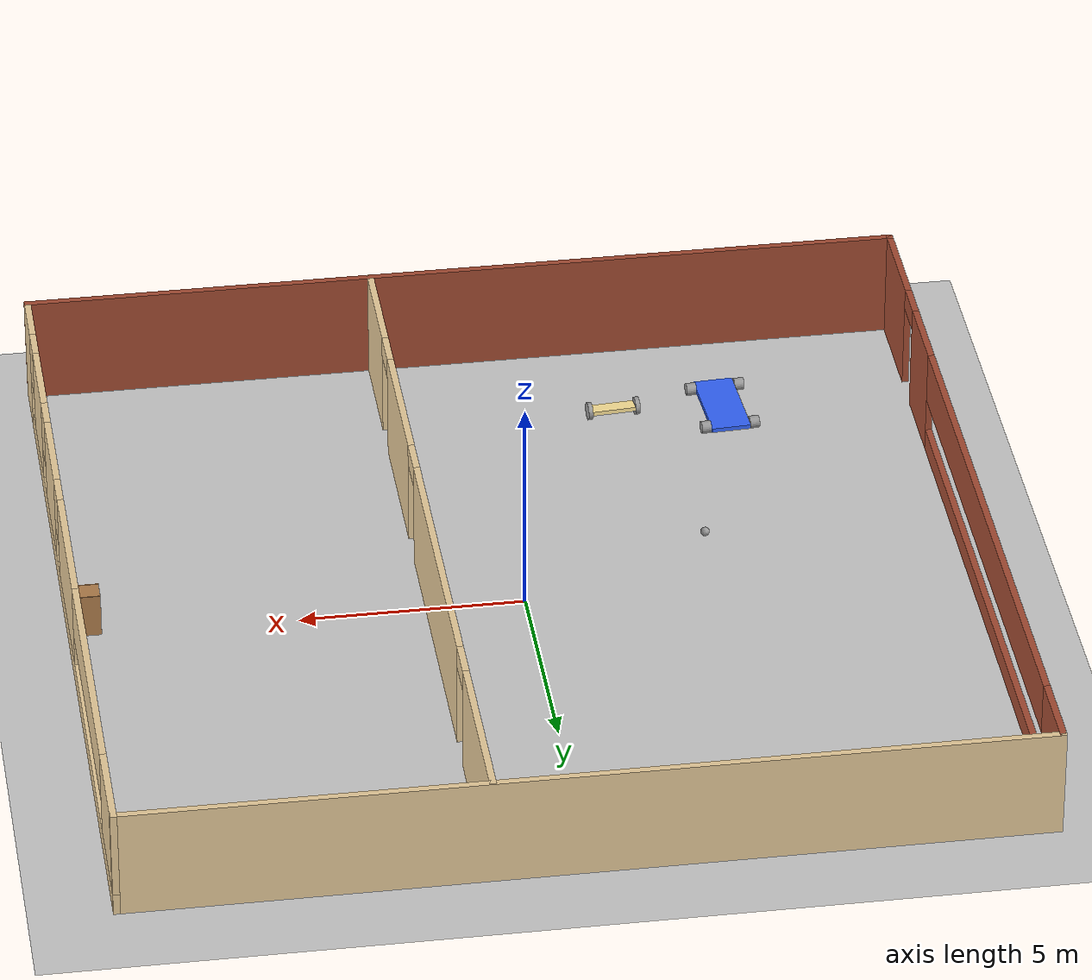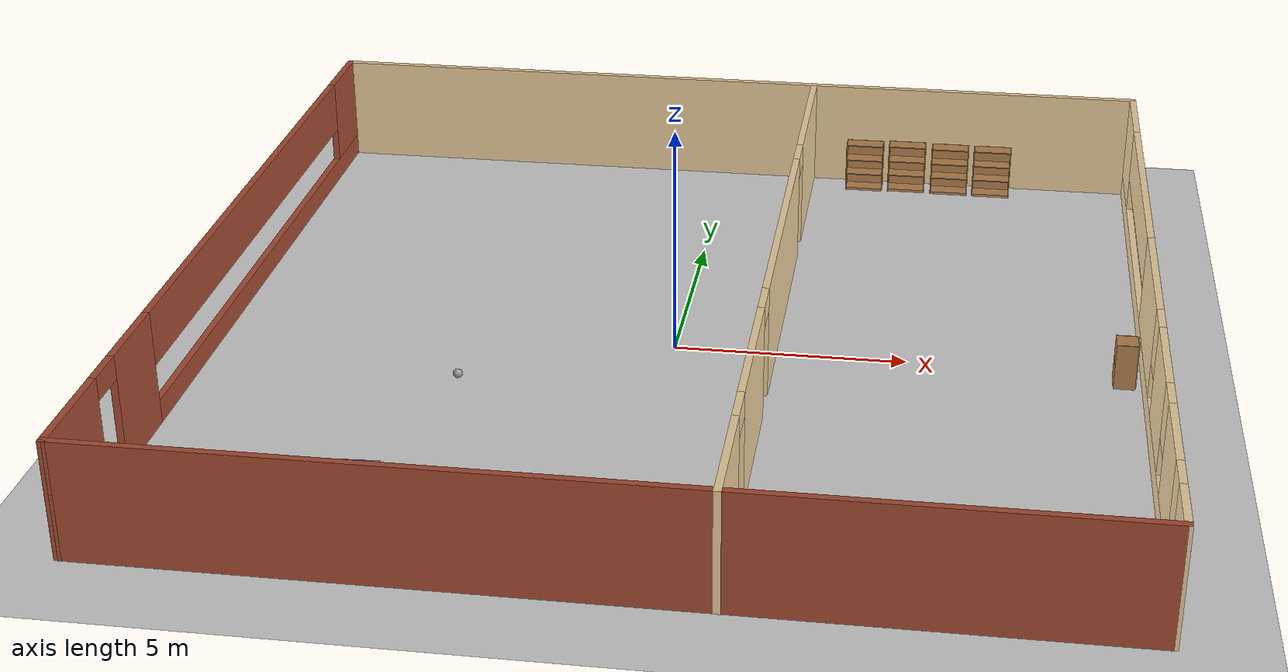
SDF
<sdf version="1.6">
 <world name="default">
  <light name="sun" type="directional">
   <pose>0 0 10 0 -0 0</pose>
   <diffuse>0.8 0.8 0.8 1</diffuse>
   <specular>0.1 0.1 0.1 1</specular>
   <attenuation>
    <range>1000</range>
    <constant>0.9</constant>
    <linear>0.01</linear>
    <quadratic>0.001</quadratic>
   </attenuation>
   <direction>-0.5 0.5 -1</direction>
  </light>
  <model name="ground_plane">
   <static>1</static>
   <link name="link">
    <collision name="collision">
     <geometry><plane><normal>0 0 1</normal><size>100 100</size></plane></geometry>
     <surface><friction><ode><mu>100</mu><mu2>50</mu2></ode></friction></surface>
    </collision>
    <visual name="visual">
     <cast_shadows>0</cast_shadows>
     <geometry><plane><normal>0 0 1</normal><size>100 100</size></plane></geometry>
     <material>
      <script><uri>file://media/materials/scripts/gazebo.material</uri><name>Gazebo/Grey</name></script>
     </material>
    </visual>
   </link>
  </model>
  <gravity>0 0 -9.8</gravity>
  <magnetic_field>6e-06 2.3e-05 -4.2e-05</magnetic_field>
  <atmosphere type="adiabatic"/>
  <physics name="default_physics" default="0" type="ode">
   <max_step_size>0.001</max_step_size>
   <real_time_factor>1</real_time_factor>
   <real_time_update_rate>1000</real_time_update_rate>
  </physics>
  <scene><ambient>0.4 0.4 0.4 1</ambient><background>0.7 0.7 0.7 1</background><shadows>1</shadows></scene>
  <spherical_coordinates>
   <surface_model>EARTH_WGS84</surface_model>
   <latitude_deg>0</latitude_deg>
   <longitude_deg>0</longitude_deg>
   <elevation>0</elevation>
   <heading_deg>0</heading_deg>
  </spherical_coordinates>
  <model name="robot">
   <link name="link_0">
    <inertial>
     <mass>1.59387</mass>
     <inertia>
      <ixx>0.470249</ixx>
      <ixy>0</ixy>
      <ixz>0</ixz>
      <iyy>0.265646</iyy>
      <iyz>0</iyz>
      <izz>0.470249</izz>
     </inertia>
    </inertial>
    <visual name="visual">
     <geometry><box><size>0.3 1 0.1</size></box></geometry>
     <material>
      <lighting>1</lighting>
      <script><uri>file://media/materials/scripts/gazebo.material</uri><name>Gazebo/Grey</name></script>
      <ambient>1 0.9 0.6 1</ambient>
      <diffuse>1 0.9 0.6 1</diffuse>
      <specular>0.01 0.01 0.01 1</specular>
      <emissive>0 0 0 1</emissive>
      <shader type="vertex"><normal_map>__default__</normal_map></shader>
     </material>
    </visual>
    <collision name="collision">
     <geometry><box><size>0.3 1 0.1</size></box></geometry>
     <surface>
      <friction>
       <ode><mu>1</mu><mu2>1</mu2><fdir1>0 0 0</fdir1><slip1>0</slip1><slip2>0</slip2></ode>
       <torsional>
        <coefficient>1</coefficient>
        <patch_radius>0</patch_radius>
        <surface_radius>0</surface_radius>
        <use_patch_radius>1</use_patch_radius>
        <ode><slip>0</slip></ode>
       </torsional>
      </friction>
      <bounce><restitution_coefficient>0</restitution_coefficient><threshold>1e+06</threshold></bounce>
      <contact>
       <collide_without_contact>0</collide_without_contact>
       <collide_without_contact_bitmask>1</collide_without_contact_bitmask>
       <collide_bitmask>1</collide_bitmask>
       <ode>
        <soft_cfm>0</soft_cfm>
        <soft_erp>0.2</soft_erp>
        <kp>1e+13</kp>
        <kd>1</kd>
        <max_vel>0.01</max_vel>
        <min_depth>0</min_depth>
       </ode>
       <bullet>
        <split_impulse>1</split_impulse>
        <split_impulse_penetration_threshold>-0.01</split_impulse_penetration_threshold>
        <soft_cfm>0</soft_cfm>
        <soft_erp>0.2</soft_erp>
        <kp>1e+13</kp>
        <kd>1</kd>
       </bullet>
      </contact>
     </surface>
    </collision>
   </link>
   <link name="link_1">
    <pose>0 -0.550019 -0 1.5707 -0 0</pose>
    <inertial>
     <mass>1</mass>
     <inertia><ixx>0.145833</ixx><ixy>0</ixy><ixz>0</ixz><iyy>0.145833</iyy><iyz>0</iyz><izz>0.125</izz></inertia>
    </inertial>
    <visual name="visual">
     <geometry><cylinder><radius>0.2</radius><length>0.1</length></cylinder></geometry>
     <material>
      <lighting>1</lighting>
      <script><uri>file://media/materials/scripts/gazebo.material</uri><name>Gazebo/Grey</name></script>
      <ambient>0.5 0.5 0.5 1</ambient>
      <diffuse>0.5 0.5 0.5 1</diffuse>
      <specular>0.01 0.01 0.01 1</specular>
      <emissive>0 0 0 1</emissive>
      <shader type="vertex"><normal_map>__default__</normal_map></shader>
     </material>
    </visual>
    <collision name="collision">
     <geometry><cylinder><radius>0.2</radius><length>0.1</length></cylinder></geometry>
     <surface>
      <friction>
       <ode><mu>1</mu><mu2>1</mu2><fdir1>0 0 0</fdir1><slip1>0</slip1><slip2>0</slip2></ode>
       <torsional>
        <coefficient>1</coefficient>
        <patch_radius>0</patch_radius>
        <surface_radius>0</surface_radius>
        <use_patch_radius>1</use_patch_radius>
        <ode><slip>0</slip></ode>
       </torsional>
      </friction>
      <bounce><restitution_coefficient>0</restitution_coefficient><threshold>1e+06</threshold></bounce>
      <contact>
       <collide_without_contact>0</collide_without_contact>
       <collide_without_contact_bitmask>1</collide_without_contact_bitmask>
       <collide_bitmask>1</collide_bitmask>
       <ode>
        <soft_cfm>0</soft_cfm>
        <soft_erp>0.2</soft_erp>
        <kp>1e+13</kp>
        <kd>1</kd>
        <max_vel>0.01</max_vel>
        <min_depth>0</min_depth>
       </ode>
       <bullet>
        <split_impulse>1</split_impulse>
        <split_impulse_penetration_threshold>-0.01</split_impulse_penetration_threshold>
        <soft_cfm>0</soft_cfm>
        <soft_erp>0.2</soft_erp>
        <kp>1e+13</kp>
        <kd>1</kd>
       </bullet>
      </contact>
     </surface>
    </collision>
   </link>
   <link name="link_1_clone">
    <pose>-0 0.550019 0 1.5707 -0 0</pose>
    <inertial>
     <mass>1</mass>
     <inertia><ixx>0.145833</ixx><ixy>0</ixy><ixz>0</ixz><iyy>0.145833</iyy><iyz>0</iyz><izz>0.125</izz></inertia>
    </inertial>
    <visual name="visual">
     <geometry><cylinder><radius>0.2</radius><length>0.1</length></cylinder></geometry>
     <material>
      <lighting>1</lighting>
      <script><uri>file://media/materials/scripts/gazebo.material</uri><name>Gazebo/Grey</name></script>
      <ambient>0.5 0.5 0.5 1</ambient>
      <diffuse>0.5 0.5 0.5 1</diffuse>
      <specular>0.01 0.01 0.01 1</specular>
      <emissive>0 0 0 1</emissive>
      <shader type="vertex"><normal_map>__default__</normal_map></shader>
     </material>
    </visual>
    <collision name="collision">
     <geometry><cylinder><radius>0.2</radius><length>0.1</length></cylinder></geometry>
     <surface>
      <friction>
       <ode><mu>1</mu><mu2>1</mu2><fdir1>0 0 0</fdir1><slip1>0</slip1><slip2>0</slip2></ode>
       <torsional>
        <coefficient>1</coefficient>
        <patch_radius>0</patch_radius>
        <surface_radius>0</surface_radius>
        <use_patch_radius>1</use_patch_radius>
        <ode><slip>0</slip></ode>
       </torsional>
      </friction>
      <bounce><restitution_coefficient>0</restitution_coefficient><threshold>1e+06</threshold></bounce>
      <contact>
       <collide_without_contact>0</collide_without_contact>
       <collide_without_contact_bitmask>1</collide_without_contact_bitmask>
       <collide_bitmask>1</collide_bitmask>
       <ode>
        <soft_cfm>0</soft_cfm>
        <soft_erp>0.2</soft_erp>
        <kp>1e+13</kp>
        <kd>1</kd>
        <max_vel>0.01</max_vel>
        <min_depth>0</min_depth>
       </ode>
       <bullet>
        <split_impulse>1</split_impulse>
        <split_impulse_penetration_threshold>-0.01</split_impulse_penetration_threshold>
        <soft_cfm>0</soft_cfm>
        <soft_erp>0.2</soft_erp>
        <kp>1e+13</kp>
        <kd>1</kd>
       </bullet>
      </contact>
     </surface>
    </collision>
   </link>
   <joint name="link_0_JOINT_0" type="revolute">
    <parent>link_0</parent>
    <child>link_1</child>
    <axis>
     <xyz>0 0 1</xyz>
     <use_parent_model_frame>0</use_parent_model_frame>
     <limit>
      <lower>-1.79769e+308</lower>
      <upper>1.79769e+308</upper>
      <effort>-1</effort>
      <velocity>-1</velocity>
     </limit>
     <dynamics>
      <spring_reference>0</spring_reference>
      <spring_stiffness>0</spring_stiffness>
      <damping>0</damping>
      <friction>0</friction>
     </dynamics>
    </axis>
    <physics>
     <ode><limit><cfm>0</cfm><erp>0.2</erp></limit><suspension><cfm>0</cfm><erp>0.2</erp></suspension></ode>
    </physics>
   </joint>
   <joint name="link_0_JOINT_1" type="revolute">
    <parent>link_0</parent>
    <child>link_1_clone</child>
    <axis>
     <xyz>0 0 1</xyz>
     <use_parent_model_frame>0</use_parent_model_frame>
     <limit>
      <lower>-1.79769e+308</lower>
      <upper>1.79769e+308</upper>
      <effort>-1</effort>
      <velocity>-1</velocity>
     </limit>
     <dynamics>
      <spring_reference>0</spring_reference>
      <spring_stiffness>0</spring_stiffness>
      <damping>0</damping>
      <friction>0</friction>
     </dynamics>
    </axis>
    <physics>
     <ode><limit><cfm>0</cfm><erp>0.2</erp></limit><suspension><cfm>0</cfm><erp>0.2</erp></suspension></ode>
    </physics>
   </joint>
   <static>0</static>
   <pose>-3.05771 -7.11011 0.200002 4e-06 -0.001771 1.64457</pose>
  </model>
  <model name="kart_0">
   <link name="link_0">
    <pose>1e-06 -0.118472 0 0 -0 0</pose>
    <inertial>
     <mass>1.59387</mass>
     <inertia>
      <ixx>0.470249</ixx>
      <ixy>0</ixy>
      <ixz>0</ixz>
      <iyy>0.265646</iyy>
      <iyz>0</iyz>
      <izz>0.470249</izz>
     </inertia>
    </inertial>
    <visual name="visual">
     <geometry><box><size>2 0.9 0.1</size></box></geometry>
     <material>
      <lighting>1</lighting>
      <script><uri>file://media/materials/scripts/gazebo.material</uri><name>Gazebo/Grey</name></script>
      <ambient>0.2 0.4 1 1</ambient>
      <diffuse>0.2 0.4 1 1</diffuse>
      <specular>0.01 0.01 0.01 1</specular>
      <emissive>0 0 0 1</emissive>
      <shader type="vertex"><normal_map>__default__</normal_map></shader>
     </material>
    </visual>
    <collision name="collision">
     <geometry><box><size>2 0.9 0.1</size></box></geometry>
     <surface>
      <friction>
       <ode><mu>1</mu><mu2>1</mu2><fdir1>0 0 0</fdir1><slip1>0</slip1><slip2>0</slip2></ode>
       <torsional>
        <coefficient>1</coefficient>
        <patch_radius>0</patch_radius>
        <surface_radius>0</surface_radius>
        <use_patch_radius>1</use_patch_radius>
        <ode><slip>0</slip></ode>
       </torsional>
      </friction>
      <bounce><restitution_coefficient>0</restitution_coefficient><threshold>1e+06</threshold></bounce>
      <contact>
       <collide_without_contact>0</collide_without_contact>
       <collide_without_contact_bitmask>1</collide_without_contact_bitmask>
       <collide_bitmask>1</collide_bitmask>
       <ode>
        <soft_cfm>0</soft_cfm>
        <soft_erp>0.2</soft_erp>
        <kp>1e+13</kp>
        <kd>1</kd>
        <max_vel>0.01</max_vel>
        <min_depth>0</min_depth>
       </ode>
       <bullet>
        <split_impulse>1</split_impulse>
        <split_impulse_penetration_threshold>-0.01</split_impulse_penetration_threshold>
        <soft_cfm>0</soft_cfm>
        <soft_erp>0.2</soft_erp>
        <kp>1e+13</kp>
        <kd>1</kd>
       </bullet>
      </contact>
     </surface>
    </collision>
   </link>
   <link name="link_1">
    <pose>-0.81362 -0.678506 9e-06 1.5707 -0 0</pose>
    <inertial>
     <mass>1</mass>
     <inertia><ixx>0.145833</ixx><ixy>0</ixy><ixz>0</ixz><iyy>0.145833</iyy><iyz>0</iyz><izz>0.125</izz></inertia>
    </inertial>
    <visual name="visual">
     <geometry><cylinder><radius>0.14</radius><length>0.22</length></cylinder></geometry>
     <material>
      <lighting>1</lighting>
      <script><uri>file://media/materials/scripts/gazebo.material</uri><name>Gazebo/Grey</name></script>
      <ambient>0.1 0.1 0.1 1</ambient>
      <diffuse>0.1 0.1 0.1 1</diffuse>
      <specular>0.01 0.01 0.01 1</specular>
      <emissive>0 0 0 1</emissive>
      <shader type="vertex"><normal_map>__default__</normal_map></shader>
     </material>
    </visual>
    <collision name="collision">
     <geometry><cylinder><radius>0.14</radius><length>0.22</length></cylinder></geometry>
     <surface>
      <friction>
       <ode><mu>1</mu><mu2>1</mu2><fdir1>0 0 0</fdir1><slip1>0</slip1><slip2>0</slip2></ode>
       <torsional>
        <coefficient>1</coefficient>
        <patch_radius>0</patch_radius>
        <surface_radius>0</surface_radius>
        <use_patch_radius>1</use_patch_radius>
        <ode><slip>0</slip></ode>
       </torsional>
      </friction>
      <bounce><restitution_coefficient>0</restitution_coefficient><threshold>1e+06</threshold></bounce>
      <contact>
       <collide_without_contact>0</collide_without_contact>
       <collide_without_contact_bitmask>1</collide_without_contact_bitmask>
       <collide_bitmask>1</collide_bitmask>
       <ode>
        <soft_cfm>0</soft_cfm>
        <soft_erp>0.2</soft_erp>
        <kp>1e+13</kp>
        <kd>1</kd>
        <max_vel>0.01</max_vel>
        <min_depth>0</min_depth>
       </ode>
       <bullet>
        <split_impulse>1</split_impulse>
        <split_impulse_penetration_threshold>-0.01</split_impulse_penetration_threshold>
        <soft_cfm>0</soft_cfm>
        <soft_erp>0.2</soft_erp>
        <kp>1e+13</kp>
        <kd>1</kd>
       </bullet>
      </contact>
     </surface>
    </collision>
   </link>
   <link name="link_1_clone">
    <pose>-0.813633 0.441545 -0 1.5707 -0 0</pose>
    <inertial>
     <mass>1</mass>
     <inertia><ixx>0.145833</ixx><ixy>0</ixy><ixz>0</ixz><iyy>0.145833</iyy><iyz>0</iyz><izz>0.125</izz></inertia>
    </inertial>
    <visual name="visual">
     <geometry><cylinder><radius>0.14</radius><length>0.22</length></cylinder></geometry>
     <material>
      <lighting>1</lighting>
      <script><uri>file://media/materials/scripts/gazebo.material</uri><name>Gazebo/Grey</name></script>
      <ambient>0.1 0.1 0.1 1</ambient>
      <diffuse>0.1 0.1 0.1 1</diffuse>
      <specular>0.01 0.01 0.01 1</specular>
      <emissive>0 0 0 1</emissive>
      <shader type="vertex"><normal_map>__default__</normal_map></shader>
     </material>
    </visual>
    <collision name="collision">
     <geometry><cylinder><radius>0.14</radius><length>0.22</length></cylinder></geometry>
     <surface>
      <friction>
       <ode><mu>1</mu><mu2>1</mu2><fdir1>0 0 0</fdir1><slip1>0</slip1><slip2>0</slip2></ode>
       <torsional>
        <coefficient>1</coefficient>
        <patch_radius>0</patch_radius>
        <surface_radius>0</surface_radius>
        <use_patch_radius>1</use_patch_radius>
        <ode><slip>0</slip></ode>
       </torsional>
      </friction>
      <bounce><restitution_coefficient>0</restitution_coefficient><threshold>1e+06</threshold></bounce>
      <contact>
       <collide_without_contact>0</collide_without_contact>
       <collide_without_contact_bitmask>1</collide_without_contact_bitmask>
       <collide_bitmask>1</collide_bitmask>
       <ode>
        <soft_cfm>0</soft_cfm>
        <soft_erp>0.2</soft_erp>
        <kp>1e+13</kp>
        <kd>1</kd>
        <max_vel>0.01</max_vel>
        <min_depth>0</min_depth>
       </ode>
       <bullet>
        <split_impulse>1</split_impulse>
        <split_impulse_penetration_threshold>-0.01</split_impulse_penetration_threshold>
        <soft_cfm>0</soft_cfm>
        <soft_erp>0.2</soft_erp>
        <kp>1e+13</kp>
        <kd>1</kd>
       </bullet>
      </contact>
     </surface>
    </collision>
   </link>
   <link name="link_1_clone_0">
    <pose>0.8 -0.678488 6e-06 1.5707 1.1e-05 1.1e-05</pose>
    <inertial>
     <mass>1</mass>
     <inertia><ixx>0.145833</ixx><ixy>0</ixy><ixz>0</ixz><iyy>0.145833</iyy><iyz>0</iyz><izz>0.125</izz></inertia>
    </inertial>
    <visual name="visual">
     <geometry><cylinder><radius>0.14</radius><length>0.22</length></cylinder></geometry>
     <material>
      <lighting>1</lighting>
      <script><uri>file://media/materials/scripts/gazebo.material</uri><name>Gazebo/Grey</name></script>
      <ambient>0.1 0.1 0.1 1</ambient>
      <diffuse>0.1 0.1 0.1 1</diffuse>
      <specular>0.01 0.01 0.01 1</specular>
      <emissive>0 0 0 1</emissive>
      <shader type="vertex"><normal_map>__default__</normal_map></shader>
     </material>
    </visual>
    <collision name="collision">
     <geometry><cylinder><radius>0.14</radius><length>0.22</length></cylinder></geometry>
     <surface>
      <friction>
       <ode><mu>1</mu><mu2>1</mu2><fdir1>0 0 0</fdir1><slip1>0</slip1><slip2>0</slip2></ode>
       <torsional>
        <coefficient>1</coefficient>
        <patch_radius>0</patch_radius>
        <surface_radius>0</surface_radius>
        <use_patch_radius>1</use_patch_radius>
        <ode><slip>0</slip></ode>
       </torsional>
      </friction>
      <bounce><restitution_coefficient>0</restitution_coefficient><threshold>1e+06</threshold></bounce>
      <contact>
       <collide_without_contact>0</collide_without_contact>
       <collide_without_contact_bitmask>1</collide_without_contact_bitmask>
       <collide_bitmask>1</collide_bitmask>
       <ode>
        <soft_cfm>0</soft_cfm>
        <soft_erp>0.2</soft_erp>
        <kp>1e+13</kp>
        <kd>1</kd>
        <max_vel>0.01</max_vel>
        <min_depth>0</min_depth>
       </ode>
       <bullet>
        <split_impulse>1</split_impulse>
        <split_impulse_penetration_threshold>-0.01</split_impulse_penetration_threshold>
        <soft_cfm>0</soft_cfm>
        <soft_erp>0.2</soft_erp>
        <kp>1e+13</kp>
        <kd>1</kd>
       </bullet>
      </contact>
     </surface>
    </collision>
   </link>
   <link name="link_1_clone_1">
    <pose>0.800005 0.441562 -2e-06 1.5707 1.1e-05 1.1e-05</pose>
    <inertial>
     <mass>1</mass>
     <inertia><ixx>0.145833</ixx><ixy>0</ixy><ixz>0</ixz><iyy>0.145833</iyy><iyz>0</iyz><izz>0.125</izz></inertia>
    </inertial>
    <visual name="visual">
     <geometry><cylinder><radius>0.14</radius><length>0.22</length></cylinder></geometry>
     <material>
      <lighting>1</lighting>
      <script><uri>file://media/materials/scripts/gazebo.material</uri><name>Gazebo/Grey</name></script>
      <ambient>0.1 0.1 0.1 1</ambient>
      <diffuse>0.1 0.1 0.1 1</diffuse>
      <specular>0.01 0.01 0.01 1</specular>
      <emissive>0 0 0 1</emissive>
      <shader type="vertex"><normal_map>__default__</normal_map></shader>
     </material>
    </visual>
    <collision name="collision">
     <geometry><cylinder><radius>0.14</radius><length>0.22</length></cylinder></geometry>
     <surface>
      <friction>
       <ode><mu>1</mu><mu2>1</mu2><fdir1>0 0 0</fdir1><slip1>0</slip1><slip2>0</slip2></ode>
       <torsional>
        <coefficient>1</coefficient>
        <patch_radius>0</patch_radius>
        <surface_radius>0</surface_radius>
        <use_patch_radius>1</use_patch_radius>
        <ode><slip>0</slip></ode>
       </torsional>
      </friction>
      <bounce><restitution_coefficient>0</restitution_coefficient><threshold>1e+06</threshold></bounce>
      <contact>
       <collide_without_contact>0</collide_without_contact>
       <collide_without_contact_bitmask>1</collide_without_contact_bitmask>
       <collide_bitmask>1</collide_bitmask>
       <ode>
        <soft_cfm>0</soft_cfm>
        <soft_erp>0.2</soft_erp>
        <kp>1e+13</kp>
        <kd>1</kd>
        <max_vel>0.01</max_vel>
        <min_depth>0</min_depth>
       </ode>
       <bullet>
        <split_impulse>1</split_impulse>
        <split_impulse_penetration_threshold>-0.01</split_impulse_penetration_threshold>
        <soft_cfm>0</soft_cfm>
        <soft_erp>0.2</soft_erp>
        <kp>1e+13</kp>
        <kd>1</kd>
       </bullet>
      </contact>
     </surface>
    </collision>
   </link>
   <joint name="link_0_JOINT_0_0" type="revolute">
    <parent>link_0</parent>
    <child>link_1_clone_0</child>
    <axis>
     <xyz>0 0 1</xyz>
     <use_parent_model_frame>0</use_parent_model_frame>
     <limit>
      <lower>-1.79769e+308</lower>
      <upper>1.79769e+308</upper>
      <effort>-1</effort>
      <velocity>-1</velocity>
     </limit>
     <dynamics>
      <spring_reference>0</spring_reference>
      <spring_stiffness>0</spring_stiffness>
      <damping>0</damping>
      <friction>0</friction>
     </dynamics>
    </axis>
    <physics>
     <ode><limit><cfm>0</cfm><erp>0.2</erp></limit><suspension><cfm>0</cfm><erp>0.2</erp></suspension></ode>
    </physics>
   </joint>
   <joint name="link_0_JOINT_0" type="revolute">
    <parent>link_0</parent>
    <child>link_1</child>
    <axis>
     <xyz>0 0 1</xyz>
     <use_parent_model_frame>0</use_parent_model_frame>
     <limit>
      <lower>-1.79769e+308</lower>
      <upper>1.79769e+308</upper>
      <effort>-1</effort>
      <velocity>-1</velocity>
     </limit>
     <dynamics>
      <spring_reference>0</spring_reference>
      <spring_stiffness>0</spring_stiffness>
      <damping>0</damping>
      <friction>0</friction>
     </dynamics>
    </axis>
    <physics>
     <ode><limit><cfm>0</cfm><erp>0.2</erp></limit><suspension><cfm>0</cfm><erp>0.2</erp></suspension></ode>
    </physics>
   </joint>
   <joint name="link_0_JOINT_1_0" type="revolute">
    <parent>link_0</parent>
    <child>link_1_clone_1</child>
    <axis>
     <xyz>1 0 0</xyz>
     <use_parent_model_frame>0</use_parent_model_frame>
     <limit>
      <lower>-1.79769e+308</lower>
      <upper>1.79769e+308</upper>
      <effort>-1</effort>
      <velocity>-1</velocity>
     </limit>
     <dynamics>
      <spring_reference>0</spring_reference>
      <spring_stiffness>0</spring_stiffness>
      <damping>0</damping>
      <friction>0</friction>
     </dynamics>
    </axis>
    <physics>
     <ode><limit><cfm>0</cfm><erp>0.2</erp></limit><suspension><cfm>0</cfm><erp>0.2</erp></suspension></ode>
    </physics>
   </joint>
   <joint name="link_0_JOINT_1" type="revolute">
    <parent>link_0</parent>
    <child>link_1_clone</child>
    <axis>
     <xyz>0 0 1</xyz>
     <use_parent_model_frame>0</use_parent_model_frame>
     <limit>
      <lower>-1.79769e+308</lower>
      <upper>1.79769e+308</upper>
      <effort>-1</effort>
      <velocity>-1</velocity>
     </limit>
     <dynamics>
      <spring_reference>0</spring_reference>
      <spring_stiffness>0</spring_stiffness>
      <damping>0</damping>
      <friction>0</friction>
     </dynamics>
    </axis>
    <physics>
     <ode><limit><cfm>0</cfm><erp>0.2</erp></limit><suspension><cfm>0</cfm><erp>0.2</erp></suspension></ode>
    </physics>
   </joint>
   <static>0</static>
   <pose>-5.44648 -6.9653 0.140001 8e-06 6e-06 -1.5163</pose>
  </model>
  <model name="bookshelf">
   <static>1</static>
   <link name="link">
    <inertial><mass>1</mass></inertial>
    <collision name="back">
     <pose>0 0.005 0.6 0 -0 0</pose>
     <geometry><box><size>0.9 0.01 1.2</size></box></geometry>
    </collision>
    <visual name="visual1">
     <pose>0 0.005 0.6 0 -0 0</pose>
     <geometry><box><size>0.9 0.01 1.2</size></box></geometry>
     <material>
      <script><uri>file://media/materials/scripts/gazebo.material</uri><name>Gazebo/Wood</name></script>
     </material>
    </visual>
    <collision name="left_side">
     <pose>0.45 -0.195 0.6 0 -0 0</pose>
     <geometry><box><size>0.02 0.4 1.2</size></box></geometry>
    </collision>
    <visual name="visual2">
     <pose>0.45 -0.195 0.6 0 -0 0</pose>
     <geometry><box><size>0.02 0.4 1.2</size></box></geometry>
     <material>
      <script><uri>file://media/materials/scripts/gazebo.material</uri><name>Gazebo/Wood</name></script>
     </material>
    </visual>
    <collision name="right_side">
     <pose>-0.45 -0.195 0.6 0 -0 0</pose>
     <geometry><box><size>0.02 0.4 1.2</size></box></geometry>
    </collision>
    <visual name="visual3">
     <pose>-0.45 -0.195 0.6 0 -0 0</pose>
     <geometry><box><size>0.02 0.4 1.2</size></box></geometry>
     <material>
      <script><uri>file://media/materials/scripts/gazebo.material</uri><name>Gazebo/Wood</name></script>
     </material>
    </visual>
    <collision name="bottom">
     <pose>0 -0.195 0.03 0 -0 0</pose>
     <geometry><box><size>0.88 0.4 0.06</size></box></geometry>
    </collision>
    <visual name="visual4">
     <pose>0 -0.195 0.03 0 -0 0</pose>
     <geometry><box><size>0.88 0.4 0.06</size></box></geometry>
     <material>
      <script><uri>file://media/materials/scripts/gazebo.material</uri><name>Gazebo/Wood</name></script>
     </material>
    </visual>
    <collision name="top">
     <pose>0 -0.195 1.19 0 -0 0</pose>
     <geometry><box><size>0.88 0.4 0.02</size></box></geometry>
    </collision>
    <visual name="visual5">
     <pose>0 -0.195 1.19 0 -0 0</pose>
     <geometry><box><size>0.88 0.4 0.02</size></box></geometry>
     <material>
      <script><uri>file://media/materials/scripts/gazebo.material</uri><name>Gazebo/Wood</name></script>
     </material>
    </visual>
    <collision name="low_shelf">
     <pose>0 -0.195 0.43 0 -0 0</pose>
     <geometry><box><size>0.88 0.4 0.02</size></box></geometry>
    </collision>
    <visual name="visual6">
     <pose>0 -0.195 0.43 0 -0 0</pose>
     <geometry><box><size>0.88 0.4 0.02</size></box></geometry>
     <material>
      <script><uri>file://media/materials/scripts/gazebo.material</uri><name>Gazebo/Wood</name></script>
     </material>
    </visual>
    <collision name="high_shelf">
     <pose>0 -0.195 0.8 0 -0 0</pose>
     <geometry><box><size>0.88 0.4 0.02</size></box></geometry>
    </collision>
    <visual name="visual7">
     <pose>0 -0.195 0.8 0 -0 0</pose>
     <geometry><box><size>0.88 0.4 0.02</size></box></geometry>
     <material>
      <script><uri>file://media/materials/scripts/gazebo.material</uri><name>Gazebo/Wood</name></script>
     </material>
    </visual>
   </link>
   <pose>3.49368 9.61547 0 0 -0 0</pose>
  </model>
  <model name="bookshelf_clone">
   <static>1</static>
   <link name="link">
    <inertial><mass>1</mass></inertial>
    <collision name="back">
     <pose>0 0.005 0.6 0 -0 0</pose>
     <geometry><box><size>0.9 0.01 1.2</size></box></geometry>
    </collision>
    <visual name="visual1">
     <pose>0 0.005 0.6 0 -0 0</pose>
     <geometry><box><size>0.9 0.01 1.2</size></box></geometry>
     <material>
      <script><uri>file://media/materials/scripts/gazebo.material</uri><name>Gazebo/Wood</name></script>
     </material>
    </visual>
    <collision name="left_side">
     <pose>0.45 -0.195 0.6 0 -0 0</pose>
     <geometry><box><size>0.02 0.4 1.2</size></box></geometry>
    </collision>
    <visual name="visual2">
     <pose>0.45 -0.195 0.6 0 -0 0</pose>
     <geometry><box><size>0.02 0.4 1.2</size></box></geometry>
     <material>
      <script><uri>file://media/materials/scripts/gazebo.material</uri><name>Gazebo/Wood</name></script>
     </material>
    </visual>
    <collision name="right_side">
     <pose>-0.45 -0.195 0.6 0 -0 0</pose>
     <geometry><box><size>0.02 0.4 1.2</size></box></geometry>
    </collision>
    <visual name="visual3">
     <pose>-0.45 -0.195 0.6 0 -0 0</pose>
     <geometry><box><size>0.02 0.4 1.2</size></box></geometry>
     <material>
      <script><uri>file://media/materials/scripts/gazebo.material</uri><name>Gazebo/Wood</name></script>
     </material>
    </visual>
    <collision name="bottom">
     <pose>0 -0.195 0.03 0 -0 0</pose>
     <geometry><box><size>0.88 0.4 0.06</size></box></geometry>
    </collision>
    <visual name="visual4">
     <pose>0 -0.195 0.03 0 -0 0</pose>
     <geometry><box><size>0.88 0.4 0.06</size></box></geometry>
     <material>
      <script><uri>file://media/materials/scripts/gazebo.material</uri><name>Gazebo/Wood</name></script>
     </material>
    </visual>
    <collision name="top">
     <pose>0 -0.195 1.19 0 -0 0</pose>
     <geometry><box><size>0.88 0.4 0.02</size></box></geometry>
    </collision>
    <visual name="visual5">
     <pose>0 -0.195 1.19 0 -0 0</pose>
     <geometry><box><size>0.88 0.4 0.02</size></box></geometry>
     <material>
      <script><uri>file://media/materials/scripts/gazebo.material</uri><name>Gazebo/Wood</name></script>
     </material>
    </visual>
    <collision name="low_shelf">
     <pose>0 -0.195 0.43 0 -0 0</pose>
     <geometry><box><size>0.88 0.4 0.02</size></box></geometry>
    </collision>
    <visual name="visual6">
     <pose>0 -0.195 0.43 0 -0 0</pose>
     <geometry><box><size>0.88 0.4 0.02</size></box></geometry>
     <material>
      <script><uri>file://media/materials/scripts/gazebo.material</uri><name>Gazebo/Wood</name></script>
     </material>
    </visual>
    <collision name="high_shelf">
     <pose>0 -0.195 0.8 0 -0 0</pose>
     <geometry><box><size>0.88 0.4 0.02</size></box></geometry>
    </collision>
    <visual name="visual7">
     <pose>0 -0.195 0.8 0 -0 0</pose>
     <geometry><box><size>0.88 0.4 0.02</size></box></geometry>
     <material>
      <script><uri>file://media/materials/scripts/gazebo.material</uri><name>Gazebo/Wood</name></script>
     </material>
    </visual>
   </link>
   <pose>4.54936 9.66295 0 0 -0 0</pose>
  </model>
  <model name="bookshelf_clone_0">
   <static>1</static>
   <link name="link">
    <inertial><mass>1</mass></inertial>
    <collision name="back">
     <pose>0 0.005 0.6 0 -0 0</pose>
     <geometry><box><size>0.9 0.01 1.2</size></box></geometry>
    </collision>
    <visual name="visual1">
     <pose>0 0.005 0.6 0 -0 0</pose>
     <geometry><box><size>0.9 0.01 1.2</size></box></geometry>
     <material>
      <script><uri>file://media/materials/scripts/gazebo.material</uri><name>Gazebo/Wood</name></script>
     </material>
    </visual>
    <collision name="left_side">
     <pose>0.45 -0.195 0.6 0 -0 0</pose>
     <geometry><box><size>0.02 0.4 1.2</size></box></geometry>
    </collision>
    <visual name="visual2">
     <pose>0.45 -0.195 0.6 0 -0 0</pose>
     <geometry><box><size>0.02 0.4 1.2</size></box></geometry>
     <material>
      <script><uri>file://media/materials/scripts/gazebo.material</uri><name>Gazebo/Wood</name></script>
     </material>
    </visual>
    <collision name="right_side">
     <pose>-0.45 -0.195 0.6 0 -0 0</pose>
     <geometry><box><size>0.02 0.4 1.2</size></box></geometry>
    </collision>
    <visual name="visual3">
     <pose>-0.45 -0.195 0.6 0 -0 0</pose>
     <geometry><box><size>0.02 0.4 1.2</size></box></geometry>
     <material>
      <script><uri>file://media/materials/scripts/gazebo.material</uri><name>Gazebo/Wood</name></script>
     </material>
    </visual>
    <collision name="bottom">
     <pose>0 -0.195 0.03 0 -0 0</pose>
     <geometry><box><size>0.88 0.4 0.06</size></box></geometry>
    </collision>
    <visual name="visual4">
     <pose>0 -0.195 0.03 0 -0 0</pose>
     <geometry><box><size>0.88 0.4 0.06</size></box></geometry>
     <material>
      <script><uri>file://media/materials/scripts/gazebo.material</uri><name>Gazebo/Wood</name></script>
     </material>
    </visual>
    <collision name="top">
     <pose>0 -0.195 1.19 0 -0 0</pose>
     <geometry><box><size>0.88 0.4 0.02</size></box></geometry>
    </collision>
    <visual name="visual5">
     <pose>0 -0.195 1.19 0 -0 0</pose>
     <geometry><box><size>0.88 0.4 0.02</size></box></geometry>
     <material>
      <script><uri>file://media/materials/scripts/gazebo.material</uri><name>Gazebo/Wood</name></script>
     </material>
    </visual>
    <collision name="low_shelf">
     <pose>0 -0.195 0.43 0 -0 0</pose>
     <geometry><box><size>0.88 0.4 0.02</size></box></geometry>
    </collision>
    <visual name="visual6">
     <pose>0 -0.195 0.43 0 -0 0</pose>
     <geometry><box><size>0.88 0.4 0.02</size></box></geometry>
     <material>
      <script><uri>file://media/materials/scripts/gazebo.material</uri><name>Gazebo/Wood</name></script>
     </material>
    </visual>
    <collision name="high_shelf">
     <pose>0 -0.195 0.8 0 -0 0</pose>
     <geometry><box><size>0.88 0.4 0.02</size></box></geometry>
    </collision>
    <visual name="visual7">
     <pose>0 -0.195 0.8 0 -0 0</pose>
     <geometry><box><size>0.88 0.4 0.02</size></box></geometry>
     <material>
      <script><uri>file://media/materials/scripts/gazebo.material</uri><name>Gazebo/Wood</name></script>
     </material>
    </visual>
   </link>
   <pose>5.61977 9.63241 0 0 -0 0</pose>
  </model>
  <model name="bookshelf_clone_1">
   <static>1</static>
   <link name="link">
    <inertial><mass>1</mass></inertial>
    <collision name="back">
     <pose>0 0.005 0.6 0 -0 0</pose>
     <geometry><box><size>0.9 0.01 1.2</size></box></geometry>
    </collision>
    <visual name="visual1">
     <pose>0 0.005 0.6 0 -0 0</pose>
     <geometry><box><size>0.9 0.01 1.2</size></box></geometry>
     <material>
      <script><uri>file://media/materials/scripts/gazebo.material</uri><name>Gazebo/Wood</name></script>
     </material>
    </visual>
    <collision name="left_side">
     <pose>0.45 -0.195 0.6 0 -0 0</pose>
     <geometry><box><size>0.02 0.4 1.2</size></box></geometry>
    </collision>
    <visual name="visual2">
     <pose>0.45 -0.195 0.6 0 -0 0</pose>
     <geometry><box><size>0.02 0.4 1.2</size></box></geometry>
     <material>
      <script><uri>file://media/materials/scripts/gazebo.material</uri><name>Gazebo/Wood</name></script>
     </material>
    </visual>
    <collision name="right_side">
     <pose>-0.45 -0.195 0.6 0 -0 0</pose>
     <geometry><box><size>0.02 0.4 1.2</size></box></geometry>
    </collision>
    <visual name="visual3">
     <pose>-0.45 -0.195 0.6 0 -0 0</pose>
     <geometry><box><size>0.02 0.4 1.2</size></box></geometry>
     <material>
      <script><uri>file://media/materials/scripts/gazebo.material</uri><name>Gazebo/Wood</name></script>
     </material>
    </visual>
    <collision name="bottom">
     <pose>0 -0.195 0.03 0 -0 0</pose>
     <geometry><box><size>0.88 0.4 0.06</size></box></geometry>
    </collision>
    <visual name="visual4">
     <pose>0 -0.195 0.03 0 -0 0</pose>
     <geometry><box><size>0.88 0.4 0.06</size></box></geometry>
     <material>
      <script><uri>file://media/materials/scripts/gazebo.material</uri><name>Gazebo/Wood</name></script>
     </material>
    </visual>
    <collision name="top">
     <pose>0 -0.195 1.19 0 -0 0</pose>
     <geometry><box><size>0.88 0.4 0.02</size></box></geometry>
    </collision>
    <visual name="visual5">
     <pose>0 -0.195 1.19 0 -0 0</pose>
     <geometry><box><size>0.88 0.4 0.02</size></box></geometry>
     <material>
      <script><uri>file://media/materials/scripts/gazebo.material</uri><name>Gazebo/Wood</name></script>
     </material>
    </visual>
    <collision name="low_shelf">
     <pose>0 -0.195 0.43 0 -0 0</pose>
     <geometry><box><size>0.88 0.4 0.02</size></box></geometry>
    </collision>
    <visual name="visual6">
     <pose>0 -0.195 0.43 0 -0 0</pose>
     <geometry><box><size>0.88 0.4 0.02</size></box></geometry>
     <material>
      <script><uri>file://media/materials/scripts/gazebo.material</uri><name>Gazebo/Wood</name></script>
     </material>
    </visual>
    <collision name="high_shelf">
     <pose>0 -0.195 0.8 0 -0 0</pose>
     <geometry><box><size>0.88 0.4 0.02</size></box></geometry>
    </collision>
    <visual name="visual7">
     <pose>0 -0.195 0.8 0 -0 0</pose>
     <geometry><box><size>0.88 0.4 0.02</size></box></geometry>
     <material>
      <script><uri>file://media/materials/scripts/gazebo.material</uri><name>Gazebo/Wood</name></script>
     </material>
    </visual>
   </link>
   <pose>6.6652 9.627 0 0 -0 0</pose>
  </model>
  <model name="cabinet">
   <static>1</static>
   <link name="cabinet_bottom_plate">
    <inertial>
     <pose>0 0 -1 0 -0 0</pose>
     <inertia><ixx>2.05</ixx><ixy>0</ixy><ixz>0</ixz><iyy>2.05</iyy><iyz>0</iyz><izz>2.05</izz></inertia>
     <mass>25</mass>
    </inertial>
    <collision name="cabinet_bottom_plate_geom">
     <pose>0 0 0.01 0 -0 0</pose>
     <geometry><box><size>0.45 0.45 0.02</size></box></geometry>
    </collision>
    <visual name="cabinet_bottom_plate_geom_visual">
     <pose>0 0 0.01 0 -0 0</pose>
     <geometry><box><size>0.45 0.45 0.02</size></box></geometry>
     <material>
      <script><uri>file://media/materials/scripts/gazebo.material</uri><name>Gazebo/Wood</name></script>
     </material>
    </visual>
    <collision name="cabinet_bottom_plate_geom_cabinet_back_plate">
     <pose>0.235 0 0.51 0 -0 0</pose>
     <geometry><box><size>0.02 0.45 1.02</size></box></geometry>
    </collision>
    <visual name="cabinet_bottom_plate_geom_cabinet_back_plate_visual">
     <pose>0.235 0 0.51 0 -0 0</pose>
     <geometry><box><size>0.02 0.45 1.02</size></box></geometry>
     <material>
      <script><uri>file://media/materials/scripts/gazebo.material</uri><name>Gazebo/Wood</name></script>
     </material>
    </visual>
    <collision name="cabinet_bottom_plate_geom_cabinet_left_plate">
     <pose>0 0.235 0.51 0 -0 0</pose>
     <geometry><box><size>0.45 0.02 1.02</size></box></geometry>
    </collision>
    <visual name="cabinet_bottom_plate_geom_cabinet_left_plate_visual">
     <pose>0 0.235 0.51 0 -0 0</pose>
     <geometry><box><size>0.45 0.02 1.02</size></box></geometry>
     <material>
      <script><uri>file://media/materials/scripts/gazebo.material</uri><name>Gazebo/Wood</name></script>
     </material>
    </visual>
    <collision name="cabinet_bottom_plate_geom_cabinet_middle_plate">
     <pose>0 0 0.51 0 -0 0</pose>
     <geometry><box><size>0.45 0.45 0.02</size></box></geometry>
    </collision>
    <visual name="cabinet_bottom_plate_geom_cabinet_middle_plate_visual">
     <pose>0 0 0.51 0 -0 0</pose>
     <geometry><box><size>0.45 0.45 0.02</size></box></geometry>
     <material>
      <script><uri>file://media/materials/scripts/gazebo.material</uri><name>Gazebo/Wood</name></script>
     </material>
    </visual>
    <collision name="cabinet_bottom_plate_geom_cabinet_right_plate">
     <pose>0 -0.235 0.51 0 -0 0</pose>
     <geometry><box><size>0.45 0.02 1.02</size></box></geometry>
    </collision>
    <visual name="cabinet_bottom_plate_geom_cabinet_right_plate_visual">
     <pose>0 -0.235 0.51 0 -0 0</pose>
     <geometry><box><size>0.45 0.02 1.02</size></box></geometry>
     <material>
      <script><uri>file://media/materials/scripts/gazebo.material</uri><name>Gazebo/Wood</name></script>
     </material>
    </visual>
    <collision name="cabinet_bottom_plate_geom_cabinet_top_plate">
     <pose>0 0 1.01 0 -0 0</pose>
     <geometry><box><size>0.45 0.45 0.02</size></box></geometry>
    </collision>
    <visual name="cabinet_bottom_plate_geom_cabinet_top_plate_visual">
     <pose>0 0 1.01 0 -0 0</pose>
     <geometry><box><size>0.45 0.45 0.02</size></box></geometry>
     <material>
      <script><uri>file://media/materials/scripts/gazebo.material</uri><name>Gazebo/Wood</name></script>
     </material>
    </visual>
   </link>
   <pose>9.56892 -0.339536 0 0 -0 0</pose>
  </model>
  <model name="whiteball">
   <link name="link_0">
    <inertial>
     <mass>1</mass>
     <inertia><ixx>0.1</ixx><ixy>0</ixy><ixz>0</ixz><iyy>0.1</iyy><iyz>0</iyz><izz>0.1</izz></inertia>
    </inertial>
    <visual name="visual">
     <geometry><sphere><radius>0.1</radius></sphere></geometry>
     <material>
      <lighting>1</lighting>
      <script><uri>file://media/materials/scripts/gazebo.material</uri><name>Gazebo/Grey</name></script>
      <shader type="pixel"><normal_map>__default__</normal_map></shader>
      <ambient>1 1 1 1</ambient>
      <diffuse>1 1 1 1</diffuse>
      <specular>1 1 1 1</specular>
      <emissive>1 1 1 1</emissive>
     </material>
    </visual>
    <collision name="collision">
     <geometry><sphere><radius>0.1</radius></sphere></geometry>
     <surface>
      <friction>
       <ode><mu>1</mu><mu2>1</mu2><fdir1>0 0 0</fdir1><slip1>0</slip1><slip2>0</slip2></ode>
       <torsional>
        <coefficient>1</coefficient>
        <patch_radius>0</patch_radius>
        <surface_radius>0</surface_radius>
        <use_patch_radius>1</use_patch_radius>
        <ode><slip>0</slip></ode>
       </torsional>
      </friction>
      <bounce><restitution_coefficient>0</restitution_coefficient><threshold>1e+06</threshold></bounce>
      <contact>
       <collide_without_contact>0</collide_without_contact>
       <collide_without_contact_bitmask>1</collide_without_contact_bitmask>
       <collide_bitmask>1</collide_bitmask>
       <ode>
        <soft_cfm>0</soft_cfm>
        <soft_erp>0.2</soft_erp>
        <kp>1e+13</kp>
        <kd>1</kd>
        <max_vel>0.01</max_vel>
        <min_depth>0</min_depth>
       </ode>
       <bullet>
        <split_impulse>1</split_impulse>
        <split_impulse_penetration_threshold>-0.01</split_impulse_penetration_threshold>
        <soft_cfm>0</soft_cfm>
        <soft_erp>0.2</soft_erp>
        <kp>1e+13</kp>
        <kd>1</kd>
       </bullet>
      </contact>
     </surface>
    </collision>
   </link>
   <static>0</static>
   <pose>-4.3489 -2.01496 0.1 0 -0 0</pose>
  </model>
  <model name="floor-blueprint">
   <link name="Wall_11">
    <pose>2.09436 -0.014107 0 0 -0 1.57213</pose>
    <visual name="Wall_11_Visual_0">
     <pose>-8.62771 0 1.25 0 -0 0</pose>
     <geometry><box><size>2.68538 0.15 2.5</size></box></geometry>
     <material>
      <script><uri>file://media/materials/scripts/gazebo.material</uri><name>Gazebo/Grey</name></script>
      <ambient>0.921569 0.807843 0.615686 1</ambient>
      <shader type="pixel"/>
      <diffuse>0.7 0.7 0.7 1</diffuse>
      <specular>0.01 0.01 0.01 1</specular>
      <emissive>0 0 0 1</emissive>
     </material>
     <meta><layer>0</layer></meta>
    </visual>
    <visual name="Wall_11_Visual_1">
     <pose>-4.6147 0 1.25 0 -0 0</pose>
     <geometry><box><size>3.54064 0.15 2.5</size></box></geometry>
     <material>
      <script><uri>file://media/materials/scripts/gazebo.material</uri><name>Gazebo/Grey</name></script>
      <ambient>0.921569 0.807843 0.615686 1</ambient>
      <shader type="pixel"/>
      <diffuse>0.7 0.7 0.7 1</diffuse>
      <specular>0.01 0.01 0.01 1</specular>
      <emissive>0 0 0 1</emissive>
     </material>
     <meta><layer>0</layer></meta>
    </visual>
    <visual name="Wall_11_Visual_2">
     <pose>1.51466 0 1.25 0 -0 0</pose>
     <geometry><box><size>6.91808 0.15 2.5</size></box></geometry>
     <material>
      <script><uri>file://media/materials/scripts/gazebo.material</uri><name>Gazebo/Grey</name></script>
      <ambient>0.921569 0.807843 0.615686 1</ambient>
      <shader type="pixel"/>
      <diffuse>0.7 0.7 0.7 1</diffuse>
      <specular>0.01 0.01 0.01 1</specular>
      <emissive>0 0 0 1</emissive>
     </material>
     <meta><layer>0</layer></meta>
    </visual>
    <visual name="Wall_11_Visual_3">
     <pose>7.92205 0 1.25 0 -0 0</pose>
     <geometry><box><size>4.09671 0.15 2.5</size></box></geometry>
     <material>
      <script><uri>file://media/materials/scripts/gazebo.material</uri><name>Gazebo/Grey</name></script>
      <ambient>0.921569 0.807843 0.615686 1</ambient>
      <shader type="pixel"/>
      <diffuse>0.7 0.7 0.7 1</diffuse>
      <specular>0.01 0.01 0.01 1</specular>
      <emissive>0 0 0 1</emissive>
     </material>
     <meta><layer>0</layer></meta>
    </visual>
    <visual name="Wall_11_Visual_4">
     <pose>-6.83502 0 2.25 0 -0 0</pose>
     <geometry><box><size>0.9 0.15 0.5</size></box></geometry>
     <material>
      <script><uri>file://media/materials/scripts/gazebo.material</uri><name>Gazebo/Grey</name></script>
      <ambient>0.921569 0.807843 0.615686 1</ambient>
      <shader type="pixel"/>
      <diffuse>0.7 0.7 0.7 1</diffuse>
      <specular>0.01 0.01 0.01 1</specular>
      <emissive>0 0 0 1</emissive>
     </material>
     <meta><layer>0</layer></meta>
    </visual>
    <visual name="Wall_11_Visual_5">
     <pose>-2.39438 0 2.25 0 -0 0</pose>
     <geometry><box><size>0.9 0.15 0.5</size></box></geometry>
     <material>
      <script><uri>file://media/materials/scripts/gazebo.material</uri><name>Gazebo/Grey</name></script>
      <ambient>0.921569 0.807843 0.615686 1</ambient>
      <shader type="pixel"/>
      <diffuse>0.7 0.7 0.7 1</diffuse>
      <specular>0.01 0.01 0.01 1</specular>
      <emissive>0 0 0 1</emissive>
     </material>
     <meta><layer>0</layer></meta>
    </visual>
    <visual name="Wall_11_Visual_6">
     <pose>5.4237 0 2.25 0 -0 0</pose>
     <geometry><box><size>0.9 0.15 0.5</size></box></geometry>
     <material>
      <script><uri>file://media/materials/scripts/gazebo.material</uri><name>Gazebo/Grey</name></script>
      <ambient>0.921569 0.807843 0.615686 1</ambient>
      <shader type="pixel"/>
      <diffuse>0.7 0.7 0.7 1</diffuse>
      <specular>0.01 0.01 0.01 1</specular>
      <emissive>0 0 0 1</emissive>
     </material>
     <meta><layer>0</layer></meta>
    </visual>
    <collision name="Wall_11_Collision_0">
     <pose>-8.62771 0 1.25 0 -0 0</pose>
     <geometry><box><size>2.68538 0.15 2.5</size></box></geometry>
     <surface>
      <friction>
       <ode><mu>1</mu><mu2>1</mu2><fdir1>0 0 0</fdir1><slip1>0</slip1><slip2>0</slip2></ode>
       <torsional>
        <coefficient>1</coefficient>
        <patch_radius>0</patch_radius>
        <surface_radius>0</surface_radius>
        <use_patch_radius>1</use_patch_radius>
        <ode><slip>0</slip></ode>
       </torsional>
      </friction>
      <bounce><restitution_coefficient>0</restitution_coefficient><threshold>1e+06</threshold></bounce>
      <contact>
       <collide_without_contact>0</collide_without_contact>
       <collide_without_contact_bitmask>1</collide_without_contact_bitmask>
       <collide_bitmask>1</collide_bitmask>
       <ode>
        <soft_cfm>0</soft_cfm>
        <soft_erp>0.2</soft_erp>
        <kp>1e+13</kp>
        <kd>1</kd>
        <max_vel>0.01</max_vel>
        <min_depth>0</min_depth>
       </ode>
       <bullet>
        <split_impulse>1</split_impulse>
        <split_impulse_penetration_threshold>-0.01</split_impulse_penetration_threshold>
        <soft_cfm>0</soft_cfm>
        <soft_erp>0.2</soft_erp>
        <kp>1e+13</kp>
        <kd>1</kd>
       </bullet>
      </contact>
     </surface>
    </collision>
    <collision name="Wall_11_Collision_1">
     <pose>-4.6147 0 1.25 0 -0 0</pose>
     <geometry><box><size>3.54064 0.15 2.5</size></box></geometry>
     <surface>
      <friction>
       <ode><mu>1</mu><mu2>1</mu2><fdir1>0 0 0</fdir1><slip1>0</slip1><slip2>0</slip2></ode>
       <torsional>
        <coefficient>1</coefficient>
        <patch_radius>0</patch_radius>
        <surface_radius>0</surface_radius>
        <use_patch_radius>1</use_patch_radius>
        <ode><slip>0</slip></ode>
       </torsional>
      </friction>
      <bounce><restitution_coefficient>0</restitution_coefficient><threshold>1e+06</threshold></bounce>
      <contact>
       <collide_without_contact>0</collide_without_contact>
       <collide_without_contact_bitmask>1</collide_without_contact_bitmask>
       <collide_bitmask>1</collide_bitmask>
       <ode>
        <soft_cfm>0</soft_cfm>
        <soft_erp>0.2</soft_erp>
        <kp>1e+13</kp>
        <kd>1</kd>
        <max_vel>0.01</max_vel>
        <min_depth>0</min_depth>
       </ode>
       <bullet>
        <split_impulse>1</split_impulse>
        <split_impulse_penetration_threshold>-0.01</split_impulse_penetration_threshold>
        <soft_cfm>0</soft_cfm>
        <soft_erp>0.2</soft_erp>
        <kp>1e+13</kp>
        <kd>1</kd>
       </bullet>
      </contact>
     </surface>
    </collision>
    <collision name="Wall_11_Collision_2">
     <pose>1.51466 0 1.25 0 -0 0</pose>
     <geometry><box><size>6.91808 0.15 2.5</size></box></geometry>
     <surface>
      <friction>
       <ode><mu>1</mu><mu2>1</mu2><fdir1>0 0 0</fdir1><slip1>0</slip1><slip2>0</slip2></ode>
       <torsional>
        <coefficient>1</coefficient>
        <patch_radius>0</patch_radius>
        <surface_radius>0</surface_radius>
        <use_patch_radius>1</use_patch_radius>
        <ode><slip>0</slip></ode>
       </torsional>
      </friction>
      <bounce><restitution_coefficient>0</restitution_coefficient><threshold>1e+06</threshold></bounce>
      <contact>
       <collide_without_contact>0</collide_without_contact>
       <collide_without_contact_bitmask>1</collide_without_contact_bitmask>
       <collide_bitmask>1</collide_bitmask>
       <ode>
        <soft_cfm>0</soft_cfm>
        <soft_erp>0.2</soft_erp>
        <kp>1e+13</kp>
        <kd>1</kd>
        <max_vel>0.01</max_vel>
        <min_depth>0</min_depth>
       </ode>
       <bullet>
        <split_impulse>1</split_impulse>
        <split_impulse_penetration_threshold>-0.01</split_impulse_penetration_threshold>
        <soft_cfm>0</soft_cfm>
        <soft_erp>0.2</soft_erp>
        <kp>1e+13</kp>
        <kd>1</kd>
       </bullet>
      </contact>
     </surface>
    </collision>
    <collision name="Wall_11_Collision_3">
     <pose>7.92205 0 1.25 0 -0 0</pose>
     <geometry><box><size>4.09671 0.15 2.5</size></box></geometry>
     <surface>
      <friction>
       <ode><mu>1</mu><mu2>1</mu2><fdir1>0 0 0</fdir1><slip1>0</slip1><slip2>0</slip2></ode>
       <torsional>
        <coefficient>1</coefficient>
        <patch_radius>0</patch_radius>
        <surface_radius>0</surface_radius>
        <use_patch_radius>1</use_patch_radius>
        <ode><slip>0</slip></ode>
       </torsional>
      </friction>
      <bounce><restitution_coefficient>0</restitution_coefficient><threshold>1e+06</threshold></bounce>
      <contact>
       <collide_without_contact>0</collide_without_contact>
       <collide_without_contact_bitmask>1</collide_without_contact_bitmask>
       <collide_bitmask>1</collide_bitmask>
       <ode>
        <soft_cfm>0</soft_cfm>
        <soft_erp>0.2</soft_erp>
        <kp>1e+13</kp>
        <kd>1</kd>
        <max_vel>0.01</max_vel>
        <min_depth>0</min_depth>
       </ode>
       <bullet>
        <split_impulse>1</split_impulse>
        <split_impulse_penetration_threshold>-0.01</split_impulse_penetration_threshold>
        <soft_cfm>0</soft_cfm>
        <soft_erp>0.2</soft_erp>
        <kp>1e+13</kp>
        <kd>1</kd>
       </bullet>
      </contact>
     </surface>
    </collision>
    <collision name="Wall_11_Collision_5">
     <pose>-2.39438 0 2.25 0 -0 0</pose>
     <geometry><box><size>0.9 0.15 0.5</size></box></geometry>
     <surface>
      <friction>
       <ode><mu>1</mu><mu2>1</mu2><fdir1>0 0 0</fdir1><slip1>0</slip1><slip2>0</slip2></ode>
       <torsional>
        <coefficient>1</coefficient>
        <patch_radius>0</patch_radius>
        <surface_radius>0</surface_radius>
        <use_patch_radius>1</use_patch_radius>
        <ode><slip>0</slip></ode>
       </torsional>
      </friction>
      <bounce><restitution_coefficient>0</restitution_coefficient><threshold>1e+06</threshold></bounce>
      <contact>
       <collide_without_contact>0</collide_without_contact>
       <collide_without_contact_bitmask>1</collide_without_contact_bitmask>
       <collide_bitmask>1</collide_bitmask>
       <ode>
        <soft_cfm>0</soft_cfm>
        <soft_erp>0.2</soft_erp>
        <kp>1e+13</kp>
        <kd>1</kd>
        <max_vel>0.01</max_vel>
        <min_depth>0</min_depth>
       </ode>
       <bullet>
        <split_impulse>1</split_impulse>
        <split_impulse_penetration_threshold>-0.01</split_impulse_penetration_threshold>
        <soft_cfm>0</soft_cfm>
        <soft_erp>0.2</soft_erp>
        <kp>1e+13</kp>
        <kd>1</kd>
       </bullet>
      </contact>
     </surface>
    </collision>
    <collision name="Wall_11_Collision_4">
     <pose>-6.83502 0 2.25 0 -0 0</pose>
     <geometry><box><size>0.9 0.15 0.5</size></box></geometry>
     <surface>
      <friction>
       <ode><mu>1</mu><mu2>1</mu2><fdir1>0 0 0</fdir1><slip1>0</slip1><slip2>0</slip2></ode>
       <torsional>
        <coefficient>1</coefficient>
        <patch_radius>0</patch_radius>
        <surface_radius>0</surface_radius>
        <use_patch_radius>1</use_patch_radius>
        <ode><slip>0</slip></ode>
       </torsional>
      </friction>
      <bounce><restitution_coefficient>0</restitution_coefficient><threshold>1e+06</threshold></bounce>
      <contact>
       <collide_without_contact>0</collide_without_contact>
       <collide_without_contact_bitmask>1</collide_without_contact_bitmask>
       <collide_bitmask>1</collide_bitmask>
       <ode>
        <soft_cfm>0</soft_cfm>
        <soft_erp>0.2</soft_erp>
        <kp>1e+13</kp>
        <kd>1</kd>
        <max_vel>0.01</max_vel>
        <min_depth>0</min_depth>
       </ode>
       <bullet>
        <split_impulse>1</split_impulse>
        <split_impulse_penetration_threshold>-0.01</split_impulse_penetration_threshold>
        <soft_cfm>0</soft_cfm>
        <soft_erp>0.2</soft_erp>
        <kp>1e+13</kp>
        <kd>1</kd>
       </bullet>
      </contact>
     </surface>
    </collision>
    <collision name="Wall_11_Collision_6">
     <pose>5.4237 0 2.25 0 -0 0</pose>
     <geometry><box><size>0.9 0.15 0.5</size></box></geometry>
     <surface>
      <friction>
       <ode><mu>1</mu><mu2>1</mu2><fdir1>0 0 0</fdir1><slip1>0</slip1><slip2>0</slip2></ode>
       <torsional>
        <coefficient>1</coefficient>
        <patch_radius>0</patch_radius>
        <surface_radius>0</surface_radius>
        <use_patch_radius>1</use_patch_radius>
        <ode><slip>0</slip></ode>
       </torsional>
      </friction>
      <bounce><restitution_coefficient>0</restitution_coefficient><threshold>1e+06</threshold></bounce>
      <contact>
       <collide_without_contact>0</collide_without_contact>
       <collide_without_contact_bitmask>1</collide_without_contact_bitmask>
       <collide_bitmask>1</collide_bitmask>
       <ode>
        <soft_cfm>0</soft_cfm>
        <soft_erp>0.2</soft_erp>
        <kp>1e+13</kp>
        <kd>1</kd>
        <max_vel>0.01</max_vel>
        <min_depth>0</min_depth>
       </ode>
       <bullet>
        <split_impulse>1</split_impulse>
        <split_impulse_penetration_threshold>-0.01</split_impulse_penetration_threshold>
        <soft_cfm>0</soft_cfm>
        <soft_erp>0.2</soft_erp>
        <kp>1e+13</kp>
        <kd>1</kd>
       </bullet>
      </contact>
     </surface>
    </collision>
   </link>
   <link name="Wall_2">
    <pose>2.1e-05 -9.90419 0 0 -0 0.000505</pose>
    <visual name="Wall_2_Visual">
     <pose>0 0 1.25 0 -0 0</pose>
     <geometry><box><size>20.1008 0.15 2.5</size></box></geometry>
     <material>
      <script><uri>file://media/materials/scripts/gazebo.material</uri><name>Gazebo/Bricks</name></script>
      <ambient>1 1 1 1</ambient>
      <shader type="pixel"/>
      <diffuse>1 1 1 1</diffuse>
      <specular>0.2 0.2 0.2 1</specular>
      <emissive>0 0 0 1</emissive>
     </material>
     <meta><layer>0</layer></meta>
    </visual>
    <collision name="Wall_2_Collision">
     <pose>0 0 1.25 0 -0 0</pose>
     <geometry><box><size>20.1008 0.15 2.5</size></box></geometry>
     <surface>
      <friction>
       <ode><mu>1</mu><mu2>1</mu2><fdir1>0 0 0</fdir1><slip1>0</slip1><slip2>0</slip2></ode>
       <torsional>
        <coefficient>1</coefficient>
        <patch_radius>0</patch_radius>
        <surface_radius>0</surface_radius>
        <use_patch_radius>1</use_patch_radius>
        <ode><slip>0</slip></ode>
       </torsional>
      </friction>
      <bounce><restitution_coefficient>0</restitution_coefficient><threshold>1e+06</threshold></bounce>
      <contact>
       <collide_without_contact>0</collide_without_contact>
       <collide_without_contact_bitmask>1</collide_without_contact_bitmask>
       <collide_bitmask>1</collide_bitmask>
       <ode>
        <soft_cfm>0</soft_cfm>
        <soft_erp>0.2</soft_erp>
        <kp>1e+13</kp>
        <kd>1</kd>
        <max_vel>0.01</max_vel>
        <min_depth>0</min_depth>
       </ode>
       <bullet>
        <split_impulse>1</split_impulse>
        <split_impulse_penetration_threshold>-0.01</split_impulse_penetration_threshold>
        <soft_cfm>0</soft_cfm>
        <soft_erp>0.2</soft_erp>
        <kp>1e+13</kp>
        <kd>1</kd>
       </bullet>
      </contact>
     </surface>
    </collision>
   </link>
   <link name="Wall_3">
    <pose>9.97471 0.005693 0 0 -0 1.57087</pose>
    <visual name="Wall_3_Visual_7">
     <pose>-5.32933 0 1.9 0 -0 0</pose>
     <geometry><box><size>0.8 0.15 1.2</size></box></geometry>
     <material>
      <script><uri>file://media/materials/scripts/gazebo.material</uri><name>Gazebo/Grey</name></script>
      <ambient>0.921569 0.807843 0.615686 1</ambient>
      <shader type="pixel"/>
      <diffuse>0.7 0.7 0.7 1</diffuse>
      <specular>0.01 0.01 0.01 1</specular>
      <emissive>0 0 0 1</emissive>
     </material>
     <meta><layer>0</layer></meta>
    </visual>
    <visual name="Wall_3_Visual_0">
     <pose>-9.28869 0 1.25 0 -0 0</pose>
     <geometry><box><size>1.38231 0.15 2.5</size></box></geometry>
     <material>
      <script><uri>file://media/materials/scripts/gazebo.material</uri><name>Gazebo/Grey</name></script>
      <ambient>0.921569 0.807843 0.615686 1</ambient>
      <shader type="pixel"/>
      <diffuse>0.7 0.7 0.7 1</diffuse>
      <specular>0.01 0.01 0.01 1</specular>
      <emissive>0 0 0 1</emissive>
     </material>
     <meta><layer>0</layer></meta>
    </visual>
    <visual name="Wall_3_Visual_1">
     <pose>0.691154 0 0.25 0 -0 0</pose>
     <geometry><box><size>18.5774 0.15 0.5</size></box></geometry>
     <material>
      <script><uri>file://media/materials/scripts/gazebo.material</uri><name>Gazebo/Grey</name></script>
      <ambient>0.921569 0.807843 0.615686 1</ambient>
      <shader type="pixel"/>
      <diffuse>0.7 0.7 0.7 1</diffuse>
      <specular>0.01 0.01 0.01 1</specular>
      <emissive>0 0 0 1</emissive>
     </material>
     <meta><layer>0</layer></meta>
    </visual>
    <visual name="Wall_3_Visual_2">
     <pose>-6.76344 0 1.5 0 -0 0</pose>
     <geometry><box><size>2.0682 0.15 2</size></box></geometry>
     <material>
      <script><uri>file://media/materials/scripts/gazebo.material</uri><name>Gazebo/Grey</name></script>
      <ambient>0.921569 0.807843 0.615686 1</ambient>
      <shader type="pixel"/>
      <diffuse>0.7 0.7 0.7 1</diffuse>
      <specular>0.01 0.01 0.01 1</specular>
      <emissive>0 0 0 1</emissive>
     </material>
     <meta><layer>0</layer></meta>
    </visual>
    <visual name="Wall_3_Visual_3">
     <pose>-3.77959 0 1.5 0 -0 0</pose>
     <geometry><box><size>2.29949 0.15 2</size></box></geometry>
     <material>
      <script><uri>file://media/materials/scripts/gazebo.material</uri><name>Gazebo/Grey</name></script>
      <ambient>0.921569 0.807843 0.615686 1</ambient>
      <shader type="pixel"/>
      <diffuse>0.7 0.7 0.7 1</diffuse>
      <specular>0.01 0.01 0.01 1</specular>
      <emissive>0 0 0 1</emissive>
     </material>
     <meta><layer>0</layer></meta>
    </visual>
    <visual name="Wall_3_Visual_4">
     <pose>-0.101831 0 1.5 0 -0 0</pose>
     <geometry><box><size>3.45603 0.15 2</size></box></geometry>
     <material>
      <script><uri>file://media/materials/scripts/gazebo.material</uri><name>Gazebo/Grey</name></script>
      <ambient>0.921569 0.807843 0.615686 1</ambient>
      <shader type="pixel"/>
      <diffuse>0.7 0.7 0.7 1</diffuse>
      <specular>0.01 0.01 0.01 1</specular>
      <emissive>0 0 0 1</emissive>
     </material>
     <meta><layer>0</layer></meta>
    </visual>
    <visual name="Wall_3_Visual_5">
     <pose>8.86304 0 1.5 0 -0 0</pose>
     <geometry><box><size>2.23361 0.15 2</size></box></geometry>
     <material>
      <script><uri>file://media/materials/scripts/gazebo.material</uri><name>Gazebo/Grey</name></script>
      <ambient>0.921569 0.807843 0.615686 1</ambient>
      <shader type="pixel"/>
      <diffuse>0.7 0.7 0.7 1</diffuse>
      <specular>0.01 0.01 0.01 1</specular>
      <emissive>0 0 0 1</emissive>
     </material>
     <meta><layer>0</layer></meta>
    </visual>
    <visual name="Wall_3_Visual_6">
     <pose>-8.19754 0 1.9 0 -0 0</pose>
     <geometry><box><size>0.8 0.15 1.2</size></box></geometry>
     <material>
      <script><uri>file://media/materials/scripts/gazebo.material</uri><name>Gazebo/Grey</name></script>
      <ambient>0.921569 0.807843 0.615686 1</ambient>
      <shader type="pixel"/>
      <diffuse>0.7 0.7 0.7 1</diffuse>
      <specular>0.01 0.01 0.01 1</specular>
      <emissive>0 0 0 1</emissive>
     </material>
     <meta><layer>0</layer></meta>
    </visual>
    <visual name="Wall_3_Visual_8">
     <pose>-2.22985 0 1.9 0 -0 0</pose>
     <geometry><box><size>0.8 0.15 1.2</size></box></geometry>
     <material>
      <script><uri>file://media/materials/scripts/gazebo.material</uri><name>Gazebo/Grey</name></script>
      <ambient>0.921569 0.807843 0.615686 1</ambient>
      <shader type="pixel"/>
      <diffuse>0.7 0.7 0.7 1</diffuse>
      <specular>0.01 0.01 0.01 1</specular>
      <emissive>0 0 0 1</emissive>
     </material>
     <meta><layer>0</layer></meta>
    </visual>
    <visual name="Wall_3_Visual_9">
     <pose>4.68621 0 1.9 0 -0 0</pose>
     <geometry><box><size>6.12005 0.15 1.2</size></box></geometry>
     <material>
      <script><uri>file://media/materials/scripts/gazebo.material</uri><name>Gazebo/Grey</name></script>
      <ambient>0.921569 0.807843 0.615686 1</ambient>
      <shader type="pixel"/>
      <diffuse>0.7 0.7 0.7 1</diffuse>
      <specular>0.01 0.01 0.01 1</specular>
      <emissive>0 0 0 1</emissive>
     </material>
     <meta><layer>0</layer></meta>
    </visual>
    <collision name="Wall_3_Collision_0">
     <pose>-9.28869 0 1.25 0 -0 0</pose>
     <geometry><box><size>1.38231 0.15 2.5</size></box></geometry>
     <surface>
      <friction>
       <ode><mu>1</mu><mu2>1</mu2><fdir1>0 0 0</fdir1><slip1>0</slip1><slip2>0</slip2></ode>
       <torsional>
        <coefficient>1</coefficient>
        <patch_radius>0</patch_radius>
        <surface_radius>0</surface_radius>
        <use_patch_radius>1</use_patch_radius>
        <ode><slip>0</slip></ode>
       </torsional>
      </friction>
      <bounce><restitution_coefficient>0</restitution_coefficient><threshold>1e+06</threshold></bounce>
      <contact>
       <collide_without_contact>0</collide_without_contact>
       <collide_without_contact_bitmask>1</collide_without_contact_bitmask>
       <collide_bitmask>1</collide_bitmask>
       <ode>
        <soft_cfm>0</soft_cfm>
        <soft_erp>0.2</soft_erp>
        <kp>1e+13</kp>
        <kd>1</kd>
        <max_vel>0.01</max_vel>
        <min_depth>0</min_depth>
       </ode>
       <bullet>
        <split_impulse>1</split_impulse>
        <split_impulse_penetration_threshold>-0.01</split_impulse_penetration_threshold>
        <soft_cfm>0</soft_cfm>
        <soft_erp>0.2</soft_erp>
        <kp>1e+13</kp>
        <kd>1</kd>
       </bullet>
      </contact>
     </surface>
    </collision>
    <collision name="Wall_3_Collision_1">
     <pose>0.691154 0 0.25 0 -0 0</pose>
     <geometry><box><size>18.5774 0.15 0.5</size></box></geometry>
     <surface>
      <friction>
       <ode><mu>1</mu><mu2>1</mu2><fdir1>0 0 0</fdir1><slip1>0</slip1><slip2>0</slip2></ode>
       <torsional>
        <coefficient>1</coefficient>
        <patch_radius>0</patch_radius>
        <surface_radius>0</surface_radius>
        <use_patch_radius>1</use_patch_radius>
        <ode><slip>0</slip></ode>
       </torsional>
      </friction>
      <bounce><restitution_coefficient>0</restitution_coefficient><threshold>1e+06</threshold></bounce>
      <contact>
       <collide_without_contact>0</collide_without_contact>
       <collide_without_contact_bitmask>1</collide_without_contact_bitmask>
       <collide_bitmask>1</collide_bitmask>
       <ode>
        <soft_cfm>0</soft_cfm>
        <soft_erp>0.2</soft_erp>
        <kp>1e+13</kp>
        <kd>1</kd>
        <max_vel>0.01</max_vel>
        <min_depth>0</min_depth>
       </ode>
       <bullet>
        <split_impulse>1</split_impulse>
        <split_impulse_penetration_threshold>-0.01</split_impulse_penetration_threshold>
        <soft_cfm>0</soft_cfm>
        <soft_erp>0.2</soft_erp>
        <kp>1e+13</kp>
        <kd>1</kd>
       </bullet>
      </contact>
     </surface>
    </collision>
    <collision name="Wall_3_Collision_4">
     <pose>-0.101831 0 1.5 0 -0 0</pose>
     <geometry><box><size>3.45603 0.15 2</size></box></geometry>
     <surface>
      <friction>
       <ode><mu>1</mu><mu2>1</mu2><fdir1>0 0 0</fdir1><slip1>0</slip1><slip2>0</slip2></ode>
       <torsional>
        <coefficient>1</coefficient>
        <patch_radius>0</patch_radius>
        <surface_radius>0</surface_radius>
        <use_patch_radius>1</use_patch_radius>
        <ode><slip>0</slip></ode>
       </torsional>
      </friction>
      <bounce><restitution_coefficient>0</restitution_coefficient><threshold>1e+06</threshold></bounce>
      <contact>
       <collide_without_contact>0</collide_without_contact>
       <collide_without_contact_bitmask>1</collide_without_contact_bitmask>
       <collide_bitmask>1</collide_bitmask>
       <ode>
        <soft_cfm>0</soft_cfm>
        <soft_erp>0.2</soft_erp>
        <kp>1e+13</kp>
        <kd>1</kd>
        <max_vel>0.01</max_vel>
        <min_depth>0</min_depth>
       </ode>
       <bullet>
        <split_impulse>1</split_impulse>
        <split_impulse_penetration_threshold>-0.01</split_impulse_penetration_threshold>
        <soft_cfm>0</soft_cfm>
        <soft_erp>0.2</soft_erp>
        <kp>1e+13</kp>
        <kd>1</kd>
       </bullet>
      </contact>
     </surface>
    </collision>
    <collision name="Wall_3_Collision_2">
     <pose>-6.76344 0 1.5 0 -0 0</pose>
     <geometry><box><size>2.0682 0.15 2</size></box></geometry>
     <surface>
      <friction>
       <ode><mu>1</mu><mu2>1</mu2><fdir1>0 0 0</fdir1><slip1>0</slip1><slip2>0</slip2></ode>
       <torsional>
        <coefficient>1</coefficient>
        <patch_radius>0</patch_radius>
        <surface_radius>0</surface_radius>
        <use_patch_radius>1</use_patch_radius>
        <ode><slip>0</slip></ode>
       </torsional>
      </friction>
      <bounce><restitution_coefficient>0</restitution_coefficient><threshold>1e+06</threshold></bounce>
      <contact>
       <collide_without_contact>0</collide_without_contact>
       <collide_without_contact_bitmask>1</collide_without_contact_bitmask>
       <collide_bitmask>1</collide_bitmask>
       <ode>
        <soft_cfm>0</soft_cfm>
        <soft_erp>0.2</soft_erp>
        <kp>1e+13</kp>
        <kd>1</kd>
        <max_vel>0.01</max_vel>
        <min_depth>0</min_depth>
       </ode>
       <bullet>
        <split_impulse>1</split_impulse>
        <split_impulse_penetration_threshold>-0.01</split_impulse_penetration_threshold>
        <soft_cfm>0</soft_cfm>
        <soft_erp>0.2</soft_erp>
        <kp>1e+13</kp>
        <kd>1</kd>
       </bullet>
      </contact>
     </surface>
    </collision>
    <collision name="Wall_3_Collision_3">
     <pose>-3.77959 0 1.5 0 -0 0</pose>
     <geometry><box><size>2.29949 0.15 2</size></box></geometry>
     <surface>
      <friction>
       <ode><mu>1</mu><mu2>1</mu2><fdir1>0 0 0</fdir1><slip1>0</slip1><slip2>0</slip2></ode>
       <torsional>
        <coefficient>1</coefficient>
        <patch_radius>0</patch_radius>
        <surface_radius>0</surface_radius>
        <use_patch_radius>1</use_patch_radius>
        <ode><slip>0</slip></ode>
       </torsional>
      </friction>
      <bounce><restitution_coefficient>0</restitution_coefficient><threshold>1e+06</threshold></bounce>
      <contact>
       <collide_without_contact>0</collide_without_contact>
       <collide_without_contact_bitmask>1</collide_without_contact_bitmask>
       <collide_bitmask>1</collide_bitmask>
       <ode>
        <soft_cfm>0</soft_cfm>
        <soft_erp>0.2</soft_erp>
        <kp>1e+13</kp>
        <kd>1</kd>
        <max_vel>0.01</max_vel>
        <min_depth>0</min_depth>
       </ode>
       <bullet>
        <split_impulse>1</split_impulse>
        <split_impulse_penetration_threshold>-0.01</split_impulse_penetration_threshold>
        <soft_cfm>0</soft_cfm>
        <soft_erp>0.2</soft_erp>
        <kp>1e+13</kp>
        <kd>1</kd>
       </bullet>
      </contact>
     </surface>
    </collision>
    <collision name="Wall_3_Collision_5">
     <pose>8.86304 0 1.5 0 -0 0</pose>
     <geometry><box><size>2.23361 0.15 2</size></box></geometry>
     <surface>
      <friction>
       <ode><mu>1</mu><mu2>1</mu2><fdir1>0 0 0</fdir1><slip1>0</slip1><slip2>0</slip2></ode>
       <torsional>
        <coefficient>1</coefficient>
        <patch_radius>0</patch_radius>
        <surface_radius>0</surface_radius>
        <use_patch_radius>1</use_patch_radius>
        <ode><slip>0</slip></ode>
       </torsional>
      </friction>
      <bounce><restitution_coefficient>0</restitution_coefficient><threshold>1e+06</threshold></bounce>
      <contact>
       <collide_without_contact>0</collide_without_contact>
       <collide_without_contact_bitmask>1</collide_without_contact_bitmask>
       <collide_bitmask>1</collide_bitmask>
       <ode>
        <soft_cfm>0</soft_cfm>
        <soft_erp>0.2</soft_erp>
        <kp>1e+13</kp>
        <kd>1</kd>
        <max_vel>0.01</max_vel>
        <min_depth>0</min_depth>
       </ode>
       <bullet>
        <split_impulse>1</split_impulse>
        <split_impulse_penetration_threshold>-0.01</split_impulse_penetration_threshold>
        <soft_cfm>0</soft_cfm>
        <soft_erp>0.2</soft_erp>
        <kp>1e+13</kp>
        <kd>1</kd>
       </bullet>
      </contact>
     </surface>
    </collision>
    <collision name="Wall_3_Collision_6">
     <pose>-8.19754 0 1.9 0 -0 0</pose>
     <geometry><box><size>0.8 0.15 1.2</size></box></geometry>
     <surface>
      <friction>
       <ode><mu>1</mu><mu2>1</mu2><fdir1>0 0 0</fdir1><slip1>0</slip1><slip2>0</slip2></ode>
       <torsional>
        <coefficient>1</coefficient>
        <patch_radius>0</patch_radius>
        <surface_radius>0</surface_radius>
        <use_patch_radius>1</use_patch_radius>
        <ode><slip>0</slip></ode>
       </torsional>
      </friction>
      <bounce><restitution_coefficient>0</restitution_coefficient><threshold>1e+06</threshold></bounce>
      <contact>
       <collide_without_contact>0</collide_without_contact>
       <collide_without_contact_bitmask>1</collide_without_contact_bitmask>
       <collide_bitmask>1</collide_bitmask>
       <ode>
        <soft_cfm>0</soft_cfm>
        <soft_erp>0.2</soft_erp>
        <kp>1e+13</kp>
        <kd>1</kd>
        <max_vel>0.01</max_vel>
        <min_depth>0</min_depth>
       </ode>
       <bullet>
        <split_impulse>1</split_impulse>
        <split_impulse_penetration_threshold>-0.01</split_impulse_penetration_threshold>
        <soft_cfm>0</soft_cfm>
        <soft_erp>0.2</soft_erp>
        <kp>1e+13</kp>
        <kd>1</kd>
       </bullet>
      </contact>
     </surface>
    </collision>
    <collision name="Wall_3_Collision_8">
     <pose>-2.22985 0 1.9 0 -0 0</pose>
     <geometry><box><size>0.8 0.15 1.2</size></box></geometry>
     <surface>
      <friction>
       <ode><mu>1</mu><mu2>1</mu2><fdir1>0 0 0</fdir1><slip1>0</slip1><slip2>0</slip2></ode>
       <torsional>
        <coefficient>1</coefficient>
        <patch_radius>0</patch_radius>
        <surface_radius>0</surface_radius>
        <use_patch_radius>1</use_patch_radius>
        <ode><slip>0</slip></ode>
       </torsional>
      </friction>
      <bounce><restitution_coefficient>0</restitution_coefficient><threshold>1e+06</threshold></bounce>
      <contact>
       <collide_without_contact>0</collide_without_contact>
       <collide_without_contact_bitmask>1</collide_without_contact_bitmask>
       <collide_bitmask>1</collide_bitmask>
       <ode>
        <soft_cfm>0</soft_cfm>
        <soft_erp>0.2</soft_erp>
        <kp>1e+13</kp>
        <kd>1</kd>
        <max_vel>0.01</max_vel>
        <min_depth>0</min_depth>
       </ode>
       <bullet>
        <split_impulse>1</split_impulse>
        <split_impulse_penetration_threshold>-0.01</split_impulse_penetration_threshold>
        <soft_cfm>0</soft_cfm>
        <soft_erp>0.2</soft_erp>
        <kp>1e+13</kp>
        <kd>1</kd>
       </bullet>
      </contact>
     </surface>
    </collision>
    <collision name="Wall_3_Collision_7">
     <pose>-5.32933 0 1.9 0 -0 0</pose>
     <geometry><box><size>0.8 0.15 1.2</size></box></geometry>
     <surface>
      <friction>
       <ode><mu>1</mu><mu2>1</mu2><fdir1>0 0 0</fdir1><slip1>0</slip1><slip2>0</slip2></ode>
       <torsional>
        <coefficient>1</coefficient>
        <patch_radius>0</patch_radius>
        <surface_radius>0</surface_radius>
        <use_patch_radius>1</use_patch_radius>
        <ode><slip>0</slip></ode>
       </torsional>
      </friction>
      <bounce><restitution_coefficient>0</restitution_coefficient><threshold>1e+06</threshold></bounce>
      <contact>
       <collide_without_contact>0</collide_without_contact>
       <collide_without_contact_bitmask>1</collide_without_contact_bitmask>
       <collide_bitmask>1</collide_bitmask>
       <ode>
        <soft_cfm>0</soft_cfm>
        <soft_erp>0.2</soft_erp>
        <kp>1e+13</kp>
        <kd>1</kd>
        <max_vel>0.01</max_vel>
        <min_depth>0</min_depth>
       </ode>
       <bullet>
        <split_impulse>1</split_impulse>
        <split_impulse_penetration_threshold>-0.01</split_impulse_penetration_threshold>
        <soft_cfm>0</soft_cfm>
        <soft_erp>0.2</soft_erp>
        <kp>1e+13</kp>
        <kd>1</kd>
       </bullet>
      </contact>
     </surface>
    </collision>
    <collision name="Wall_3_Collision_9">
     <pose>4.68621 0 1.9 0 -0 0</pose>
     <geometry><box><size>6.12005 0.15 1.2</size></box></geometry>
     <surface>
      <friction>
       <ode><mu>1</mu><mu2>1</mu2><fdir1>0 0 0</fdir1><slip1>0</slip1><slip2>0</slip2></ode>
       <torsional>
        <coefficient>1</coefficient>
        <patch_radius>0</patch_radius>
        <surface_radius>0</surface_radius>
        <use_patch_radius>1</use_patch_radius>
        <ode><slip>0</slip></ode>
       </torsional>
      </friction>
      <bounce><restitution_coefficient>0</restitution_coefficient><threshold>1e+06</threshold></bounce>
      <contact>
       <collide_without_contact>0</collide_without_contact>
       <collide_without_contact_bitmask>1</collide_without_contact_bitmask>
       <collide_bitmask>1</collide_bitmask>
       <ode>
        <soft_cfm>0</soft_cfm>
        <soft_erp>0.2</soft_erp>
        <kp>1e+13</kp>
        <kd>1</kd>
        <max_vel>0.01</max_vel>
        <min_depth>0</min_depth>
       </ode>
       <bullet>
        <split_impulse>1</split_impulse>
        <split_impulse_penetration_threshold>-0.01</split_impulse_penetration_threshold>
        <soft_cfm>0</soft_cfm>
        <soft_erp>0.2</soft_erp>
        <kp>1e+13</kp>
        <kd>1</kd>
       </bullet>
      </contact>
     </surface>
    </collision>
   </link>
   <link name="Wall_5">
    <pose>-9.96438 -0.010103 0 0 -0 1.56969</pose>
    <visual name="Wall_5_Visual_1">
     <pose>-5.72783 0 1.25 0 -0 0</pose>
     <geometry><box><size>1.87936 0.15 2.5</size></box></geometry>
     <material>
      <script><uri>file://media/materials/scripts/gazebo.material</uri><name>Gazebo/Bricks</name></script>
      <ambient>1 1 1 1</ambient>
      <shader type="pixel"/>
      <diffuse>1 1 1 1</diffuse>
      <specular>0.2 0.2 0.2 1</specular>
      <emissive>0 0 0 1</emissive>
     </material>
     <meta><layer>0</layer></meta>
    </visual>
    <visual name="Wall_5_Visual_0">
     <pose>-8.77082 0 1.25 0 -0 0</pose>
     <geometry><box><size>2.40661 0.15 2.5</size></box></geometry>
     <material>
      <script><uri>file://media/materials/scripts/gazebo.material</uri><name>Gazebo/Bricks</name></script>
      <ambient>1 1 1 1</ambient>
      <shader type="pixel"/>
      <diffuse>1 1 1 1</diffuse>
      <specular>0.2 0.2 0.2 1</specular>
      <emissive>0 0 0 1</emissive>
     </material>
     <meta><layer>0</layer></meta>
    </visual>
    <visual name="Wall_5_Visual_2">
     <pose>2.59299 0 0.25 0 -0 0</pose>
     <geometry><box><size>14.7623 0.15 0.5</size></box></geometry>
     <material>
      <script><uri>file://media/materials/scripts/gazebo.material</uri><name>Gazebo/Bricks</name></script>
      <ambient>1 1 1 1</ambient>
      <shader type="pixel"/>
      <diffuse>1 1 1 1</diffuse>
      <specular>0.2 0.2 0.2 1</specular>
      <emissive>0 0 0 1</emissive>
     </material>
     <meta><layer>0</layer></meta>
    </visual>
    <visual name="Wall_5_Visual_3">
     <pose>9.0761 0 1.5 0 -0 0</pose>
     <geometry><box><size>1.79604 0.15 2</size></box></geometry>
     <material>
      <script><uri>file://media/materials/scripts/gazebo.material</uri><name>Gazebo/Bricks</name></script>
      <ambient>1 1 1 1</ambient>
      <shader type="pixel"/>
      <diffuse>1 1 1 1</diffuse>
      <specular>0.2 0.2 0.2 1</specular>
      <emissive>0 0 0 1</emissive>
     </material>
     <meta><layer>0</layer></meta>
    </visual>
    <visual name="Wall_5_Visual_4">
     <pose>1.69496 0 1.9 0 -0 0</pose>
     <geometry><box><size>12.9662 0.15 1.2</size></box></geometry>
     <material>
      <script><uri>file://media/materials/scripts/gazebo.material</uri><name>Gazebo/Bricks</name></script>
      <ambient>1 1 1 1</ambient>
      <shader type="pixel"/>
      <diffuse>1 1 1 1</diffuse>
      <specular>0.2 0.2 0.2 1</specular>
      <emissive>0 0 0 1</emissive>
     </material>
     <meta><layer>0</layer></meta>
    </visual>
    <visual name="Wall_5_Visual_5">
     <pose>-7.11751 0 2.25 0 -0 0</pose>
     <geometry><box><size>0.9 0.15 0.5</size></box></geometry>
     <material>
      <script><uri>file://media/materials/scripts/gazebo.material</uri><name>Gazebo/Bricks</name></script>
      <ambient>1 1 1 1</ambient>
      <shader type="pixel"/>
      <diffuse>1 1 1 1</diffuse>
      <specular>0.2 0.2 0.2 1</specular>
      <emissive>0 0 0 1</emissive>
     </material>
     <meta><layer>0</layer></meta>
    </visual>
    <collision name="Wall_5_Collision_0">
     <pose>-8.77082 0 1.25 0 -0 0</pose>
     <geometry><box><size>2.40661 0.15 2.5</size></box></geometry>
     <surface>
      <friction>
       <ode><mu>1</mu><mu2>1</mu2><fdir1>0 0 0</fdir1><slip1>0</slip1><slip2>0</slip2></ode>
       <torsional>
        <coefficient>1</coefficient>
        <patch_radius>0</patch_radius>
        <surface_radius>0</surface_radius>
        <use_patch_radius>1</use_patch_radius>
        <ode><slip>0</slip></ode>
       </torsional>
      </friction>
      <bounce><restitution_coefficient>0</restitution_coefficient><threshold>1e+06</threshold></bounce>
      <contact>
       <collide_without_contact>0</collide_without_contact>
       <collide_without_contact_bitmask>1</collide_without_contact_bitmask>
       <collide_bitmask>1</collide_bitmask>
       <ode>
        <soft_cfm>0</soft_cfm>
        <soft_erp>0.2</soft_erp>
        <kp>1e+13</kp>
        <kd>1</kd>
        <max_vel>0.01</max_vel>
        <min_depth>0</min_depth>
       </ode>
       <bullet>
        <split_impulse>1</split_impulse>
        <split_impulse_penetration_threshold>-0.01</split_impulse_penetration_threshold>
        <soft_cfm>0</soft_cfm>
        <soft_erp>0.2</soft_erp>
        <kp>1e+13</kp>
        <kd>1</kd>
       </bullet>
      </contact>
     </surface>
    </collision>
    <collision name="Wall_5_Collision_1">
     <pose>-5.72783 0 1.25 0 -0 0</pose>
     <geometry><box><size>1.87936 0.15 2.5</size></box></geometry>
     <surface>
      <friction>
       <ode><mu>1</mu><mu2>1</mu2><fdir1>0 0 0</fdir1><slip1>0</slip1><slip2>0</slip2></ode>
       <torsional>
        <coefficient>1</coefficient>
        <patch_radius>0</patch_radius>
        <surface_radius>0</surface_radius>
        <use_patch_radius>1</use_patch_radius>
        <ode><slip>0</slip></ode>
       </torsional>
      </friction>
      <bounce><restitution_coefficient>0</restitution_coefficient><threshold>1e+06</threshold></bounce>
      <contact>
       <collide_without_contact>0</collide_without_contact>
       <collide_without_contact_bitmask>1</collide_without_contact_bitmask>
       <collide_bitmask>1</collide_bitmask>
       <ode>
        <soft_cfm>0</soft_cfm>
        <soft_erp>0.2</soft_erp>
        <kp>1e+13</kp>
        <kd>1</kd>
        <max_vel>0.01</max_vel>
        <min_depth>0</min_depth>
       </ode>
       <bullet>
        <split_impulse>1</split_impulse>
        <split_impulse_penetration_threshold>-0.01</split_impulse_penetration_threshold>
        <soft_cfm>0</soft_cfm>
        <soft_erp>0.2</soft_erp>
        <kp>1e+13</kp>
        <kd>1</kd>
       </bullet>
      </contact>
     </surface>
    </collision>
    <collision name="Wall_5_Collision_4">
     <pose>1.69496 0 1.9 0 -0 0</pose>
     <geometry><box><size>12.9662 0.15 1.2</size></box></geometry>
     <surface>
      <friction>
       <ode><mu>1</mu><mu2>1</mu2><fdir1>0 0 0</fdir1><slip1>0</slip1><slip2>0</slip2></ode>
       <torsional>
        <coefficient>1</coefficient>
        <patch_radius>0</patch_radius>
        <surface_radius>0</surface_radius>
        <use_patch_radius>1</use_patch_radius>
        <ode><slip>0</slip></ode>
       </torsional>
      </friction>
      <bounce><restitution_coefficient>0</restitution_coefficient><threshold>1e+06</threshold></bounce>
      <contact>
       <collide_without_contact>0</collide_without_contact>
       <collide_without_contact_bitmask>1</collide_without_contact_bitmask>
       <collide_bitmask>1</collide_bitmask>
       <ode>
        <soft_cfm>0</soft_cfm>
        <soft_erp>0.2</soft_erp>
        <kp>1e+13</kp>
        <kd>1</kd>
        <max_vel>0.01</max_vel>
        <min_depth>0</min_depth>
       </ode>
       <bullet>
        <split_impulse>1</split_impulse>
        <split_impulse_penetration_threshold>-0.01</split_impulse_penetration_threshold>
        <soft_cfm>0</soft_cfm>
        <soft_erp>0.2</soft_erp>
        <kp>1e+13</kp>
        <kd>1</kd>
       </bullet>
      </contact>
     </surface>
    </collision>
    <collision name="Wall_5_Collision_2">
     <pose>2.59299 0 0.25 0 -0 0</pose>
     <geometry><box><size>14.7623 0.15 0.5</size></box></geometry>
     <surface>
      <friction>
       <ode><mu>1</mu><mu2>1</mu2><fdir1>0 0 0</fdir1><slip1>0</slip1><slip2>0</slip2></ode>
       <torsional>
        <coefficient>1</coefficient>
        <patch_radius>0</patch_radius>
        <surface_radius>0</surface_radius>
        <use_patch_radius>1</use_patch_radius>
        <ode><slip>0</slip></ode>
       </torsional>
      </friction>
      <bounce><restitution_coefficient>0</restitution_coefficient><threshold>1e+06</threshold></bounce>
      <contact>
       <collide_without_contact>0</collide_without_contact>
       <collide_without_contact_bitmask>1</collide_without_contact_bitmask>
       <collide_bitmask>1</collide_bitmask>
       <ode>
        <soft_cfm>0</soft_cfm>
        <soft_erp>0.2</soft_erp>
        <kp>1e+13</kp>
        <kd>1</kd>
        <max_vel>0.01</max_vel>
        <min_depth>0</min_depth>
       </ode>
       <bullet>
        <split_impulse>1</split_impulse>
        <split_impulse_penetration_threshold>-0.01</split_impulse_penetration_threshold>
        <soft_cfm>0</soft_cfm>
        <soft_erp>0.2</soft_erp>
        <kp>1e+13</kp>
        <kd>1</kd>
       </bullet>
      </contact>
     </surface>
    </collision>
    <collision name="Wall_5_Collision_3">
     <pose>9.0761 0 1.5 0 -0 0</pose>
     <geometry><box><size>1.79604 0.15 2</size></box></geometry>
     <surface>
      <friction>
       <ode><mu>1</mu><mu2>1</mu2><fdir1>0 0 0</fdir1><slip1>0</slip1><slip2>0</slip2></ode>
       <torsional>
        <coefficient>1</coefficient>
        <patch_radius>0</patch_radius>
        <surface_radius>0</surface_radius>
        <use_patch_radius>1</use_patch_radius>
        <ode><slip>0</slip></ode>
       </torsional>
      </friction>
      <bounce><restitution_coefficient>0</restitution_coefficient><threshold>1e+06</threshold></bounce>
      <contact>
       <collide_without_contact>0</collide_without_contact>
       <collide_without_contact_bitmask>1</collide_without_contact_bitmask>
       <collide_bitmask>1</collide_bitmask>
       <ode>
        <soft_cfm>0</soft_cfm>
        <soft_erp>0.2</soft_erp>
        <kp>1e+13</kp>
        <kd>1</kd>
        <max_vel>0.01</max_vel>
        <min_depth>0</min_depth>
       </ode>
       <bullet>
        <split_impulse>1</split_impulse>
        <split_impulse_penetration_threshold>-0.01</split_impulse_penetration_threshold>
        <soft_cfm>0</soft_cfm>
        <soft_erp>0.2</soft_erp>
        <kp>1e+13</kp>
        <kd>1</kd>
       </bullet>
      </contact>
     </surface>
    </collision>
    <collision name="Wall_5_Collision_5">
     <pose>-7.11751 0 2.25 0 -0 0</pose>
     <geometry><box><size>0.9 0.15 0.5</size></box></geometry>
     <surface>
      <friction>
       <ode><mu>1</mu><mu2>1</mu2><fdir1>0 0 0</fdir1><slip1>0</slip1><slip2>0</slip2></ode>
       <torsional>
        <coefficient>1</coefficient>
        <patch_radius>0</patch_radius>
        <surface_radius>0</surface_radius>
        <use_patch_radius>1</use_patch_radius>
        <ode><slip>0</slip></ode>
       </torsional>
      </friction>
      <bounce><restitution_coefficient>0</restitution_coefficient><threshold>1e+06</threshold></bounce>
      <contact>
       <collide_without_contact>0</collide_without_contact>
       <collide_without_contact_bitmask>1</collide_without_contact_bitmask>
       <collide_bitmask>1</collide_bitmask>
       <ode>
        <soft_cfm>0</soft_cfm>
        <soft_erp>0.2</soft_erp>
        <kp>1e+13</kp>
        <kd>1</kd>
        <max_vel>0.01</max_vel>
        <min_depth>0</min_depth>
       </ode>
       <bullet>
        <split_impulse>1</split_impulse>
        <split_impulse_penetration_threshold>-0.01</split_impulse_penetration_threshold>
        <soft_cfm>0</soft_cfm>
        <soft_erp>0.2</soft_erp>
        <kp>1e+13</kp>
        <kd>1</kd>
       </bullet>
      </contact>
     </surface>
    </collision>
   </link>
   <link name="Wall_7">
    <pose>0.012375 9.90961 0 0 0 -3.1415</pose>
    <visual name="Wall_7_Visual">
     <pose>0 0 1.25 0 -0 0</pose>
     <geometry><box><size>20.0733 0.15 2.5</size></box></geometry>
     <material>
      <script><uri>file://media/materials/scripts/gazebo.material</uri><name>Gazebo/Grey</name></script>
      <ambient>0.921569 0.807843 0.615686 1</ambient>
      <shader type="pixel"/>
      <diffuse>0.7 0.7 0.7 1</diffuse>
      <specular>0.01 0.01 0.01 1</specular>
      <emissive>0 0 0 1</emissive>
     </material>
     <meta><layer>0</layer></meta>
    </visual>
    <collision name="Wall_7_Collision">
     <pose>0 0 1.25 0 -0 0</pose>
     <geometry><box><size>20.0733 0.15 2.5</size></box></geometry>
     <surface>
      <friction>
       <ode><mu>1</mu><mu2>1</mu2><fdir1>0 0 0</fdir1><slip1>0</slip1><slip2>0</slip2></ode>
       <torsional>
        <coefficient>1</coefficient>
        <patch_radius>0</patch_radius>
        <surface_radius>0</surface_radius>
        <use_patch_radius>1</use_patch_radius>
        <ode><slip>0</slip></ode>
       </torsional>
      </friction>
      <bounce><restitution_coefficient>0</restitution_coefficient><threshold>1e+06</threshold></bounce>
      <contact>
       <collide_without_contact>0</collide_without_contact>
       <collide_without_contact_bitmask>1</collide_without_contact_bitmask>
       <collide_bitmask>1</collide_bitmask>
       <ode>
        <soft_cfm>0</soft_cfm>
        <soft_erp>0.2</soft_erp>
        <kp>1e+13</kp>
        <kd>1</kd>
        <max_vel>0.01</max_vel>
        <min_depth>0</min_depth>
       </ode>
       <bullet>
        <split_impulse>1</split_impulse>
        <split_impulse_penetration_threshold>-0.01</split_impulse_penetration_threshold>
        <soft_cfm>0</soft_cfm>
        <soft_erp>0.2</soft_erp>
        <kp>1e+13</kp>
        <kd>1</kd>
       </bullet>
      </contact>
     </surface>
    </collision>
   </link>
   <static>1</static>
   <pose>0.039338 0.036734 0 0 -0 0</pose>
  </model>
 </world>
</sdf>
